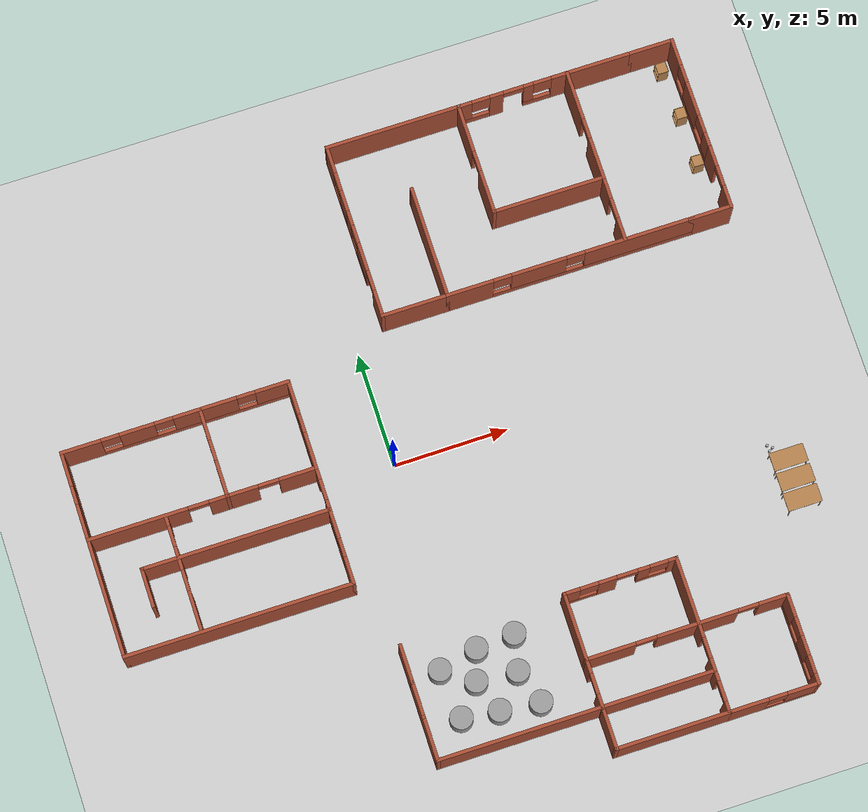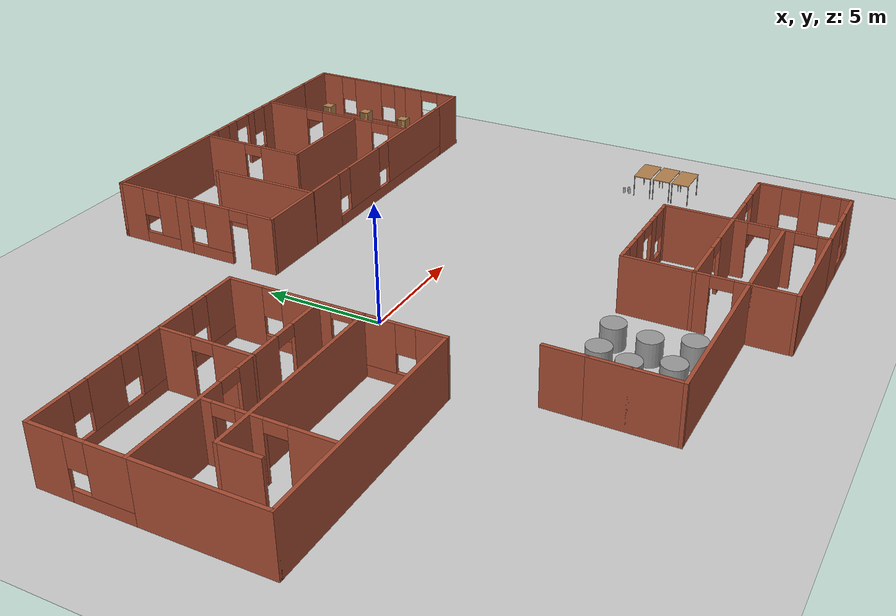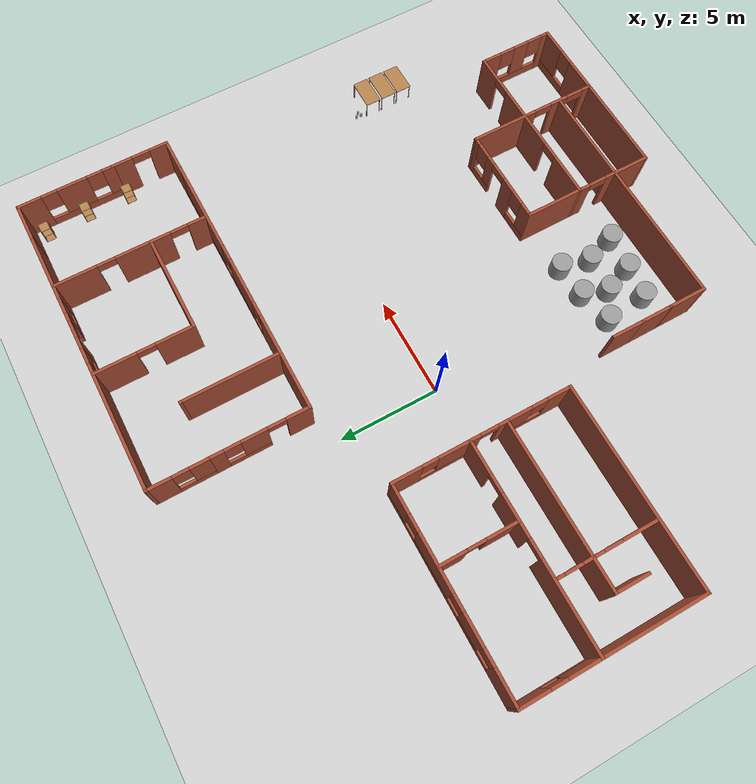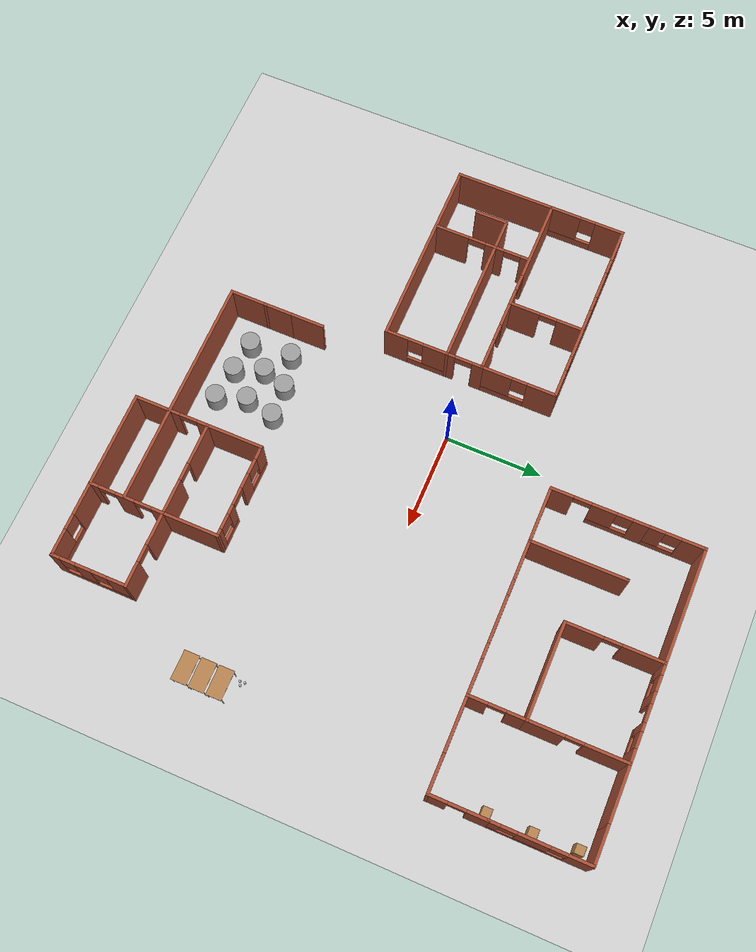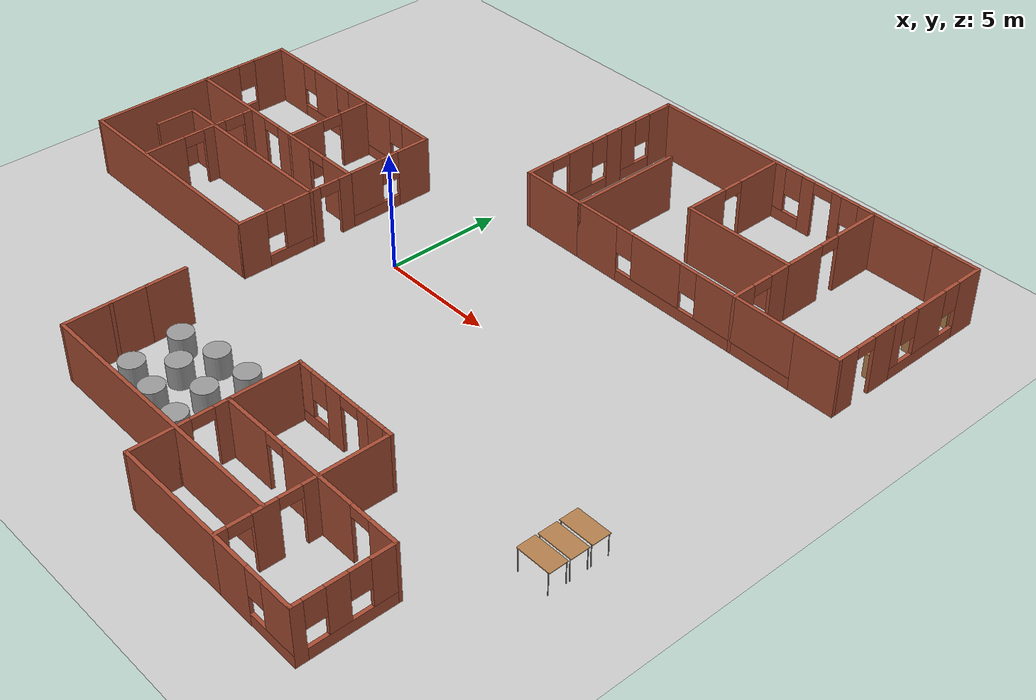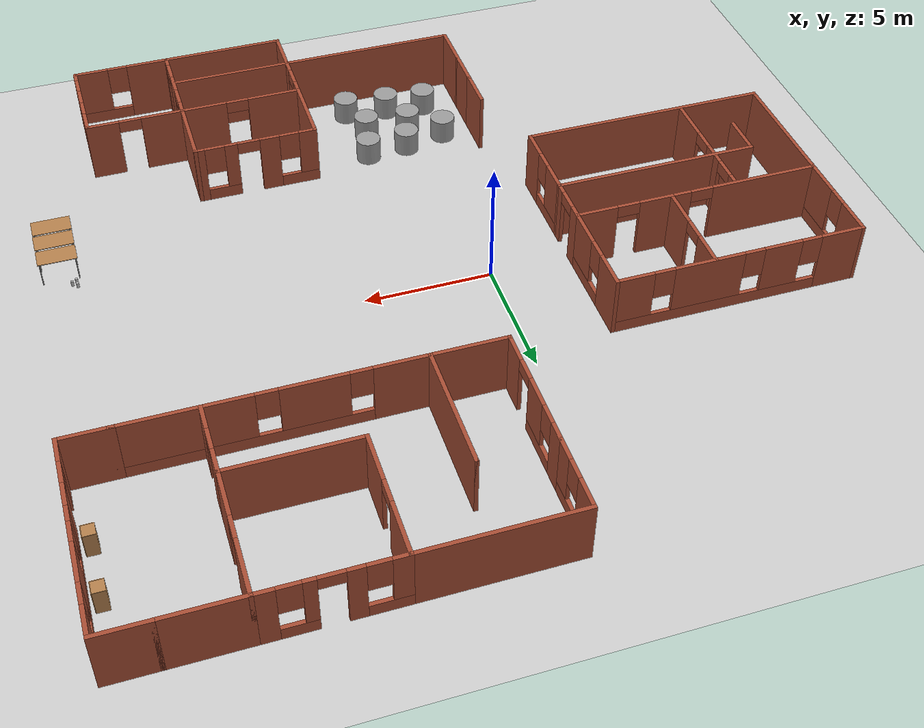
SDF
<sdf version="1.7">
 <world name="default">
  <light name="sun" type="directional">
   <pose>0 0 10 0 -0 0</pose>
   <diffuse>0.8 0.8 0.8 1</diffuse>
   <specular>0.2 0.2 0.2 1</specular>
   <attenuation>
    <range>1000</range>
    <constant>0.9</constant>
    <linear>0.01</linear>
    <quadratic>0.001</quadratic>
   </attenuation>
   <direction>-0.5 0.1 -0.9</direction>
   <spot><inner_angle>0</inner_angle><outer_angle>0</outer_angle><falloff>0</falloff></spot>
  </light>
  <model name="ground_plane">
   <static>1</static>
   <link name="link">
    <collision name="collision">
     <geometry><plane><normal>0 0 1</normal><size>100 100</size></plane></geometry>
     <surface><friction><ode><mu>100</mu><mu2>50</mu2></ode></friction></surface>
    </collision>
    <visual name="visual">
     <cast_shadows>0</cast_shadows>
     <geometry><plane><normal>0 0 1</normal><size>100 100</size></plane></geometry>
     <material>
      <script><uri>file://media/materials/scripts/gazebo.material</uri><name>Gazebo/Grey</name></script>
     </material>
    </visual>
   </link>
  </model>
  <gravity>0 0 -9.8</gravity>
  <magnetic_field>6e-06 2.3e-05 -4.2e-05</magnetic_field>
  <atmosphere type="adiabatic"/>
  <physics type="ode">
   <max_step_size>0.001</max_step_size>
   <real_time_factor>1</real_time_factor>
   <real_time_update_rate>1000</real_time_update_rate>
  </physics>
  <scene><ambient>0.85 0.5 0.125 1</ambient><background>0.7 0.7 0.7 1</background><shadows>1</shadows></scene>
  <spherical_coordinates>
   <surface_model>EARTH_WGS84</surface_model>
   <latitude_deg>0</latitude_deg>
   <longitude_deg>0</longitude_deg>
   <elevation>0</elevation>
   <heading_deg>0</heading_deg>
  </spherical_coordinates>
  <model name="Brick_house3">
   <pose>-3.01773 -0.204708 0 0 -0 0</pose>
   <link name="Wall_11">
    <pose>-10.0574 2.55 0 0 -0 -1.5708</pose>
    <visual name="Wall_11_Visual_0">
     <pose>-1.22598 0 1.25 0 -0 0</pose>
     <geometry><box><size>1.54805 0.15 2.5</size></box></geometry>
     <material>
      <script><uri>file://media/materials/scripts/gazebo.material</uri><name>Gazebo/Bricks</name></script>
      <ambient>1 1 1 1</ambient>
     </material>
     <meta><layer>0</layer></meta>
    </visual>
    <collision name="Wall_11_Collision_0">
     <geometry><box><size>1.54805 0.15 2.5</size></box></geometry>
     <pose>-1.22598 0 1.25 0 -0 0</pose>
    </collision>
    <visual name="Wall_11_Visual_1">
     <pose>0.774024 0 0.25 0 -0 0</pose>
     <geometry><box><size>2.45195 0.15 0.5</size></box></geometry>
     <material>
      <script><uri>file://media/materials/scripts/gazebo.material</uri><name>Gazebo/Bricks</name></script>
      <ambient>1 1 1 1</ambient>
     </material>
     <meta><layer>0</layer></meta>
    </visual>
    <collision name="Wall_11_Collision_1">
     <geometry><box><size>2.45195 0.15 0.5</size></box></geometry>
     <pose>0.774024 0 0.25 0 -0 0</pose>
    </collision>
    <visual name="Wall_11_Visual_2">
     <pose>1.17402 0 1.5 0 -0 0</pose>
     <geometry><box><size>1.65195 0.15 2</size></box></geometry>
     <material>
      <script><uri>file://media/materials/scripts/gazebo.material</uri><name>Gazebo/Bricks</name></script>
      <ambient>1 1 1 1</ambient>
     </material>
     <meta><layer>0</layer></meta>
    </visual>
    <collision name="Wall_11_Collision_2">
     <geometry><box><size>1.65195 0.15 2</size></box></geometry>
     <pose>1.17402 0 1.5 0 -0 0</pose>
    </collision>
    <visual name="Wall_11_Visual_3">
     <pose>-0.051953 0 1.9 0 -0 0</pose>
     <geometry><box><size>0.8 0.15 1.2</size></box></geometry>
     <material>
      <script><uri>file://media/materials/scripts/gazebo.material</uri><name>Gazebo/Bricks</name></script>
      <ambient>1 1 1 1</ambient>
     </material>
     <meta><layer>0</layer></meta>
    </visual>
    <collision name="Wall_11_Collision_3">
     <geometry><box><size>0.8 0.15 1.2</size></box></geometry>
     <pose>-0.051953 0 1.9 0 -0 0</pose>
    </collision>
   </link>
   <link name="Wall_12">
    <pose>-7.05736 0.625 0 0 -0 0</pose>
    <visual name="Wall_12_Visual_0">
     <pose>-0.888053 0 1.25 0 -0 0</pose>
     <geometry><box><size>4.3739 0.15 2.5</size></box></geometry>
     <material>
      <script><uri>file://media/materials/scripts/gazebo.material</uri><name>Gazebo/Bricks</name></script>
      <ambient>1 1 1 1</ambient>
     </material>
     <meta><layer>0</layer></meta>
    </visual>
    <collision name="Wall_12_Collision_0">
     <geometry><box><size>4.3739 0.15 2.5</size></box></geometry>
     <pose>-0.888053 0 1.25 0 -0 0</pose>
    </collision>
    <visual name="Wall_12_Visual_1">
     <pose>2.63695 0 1.25 0 -0 0</pose>
     <geometry><box><size>0.876105 0.15 2.5</size></box></geometry>
     <material>
      <script><uri>file://media/materials/scripts/gazebo.material</uri><name>Gazebo/Bricks</name></script>
      <ambient>1 1 1 1</ambient>
     </material>
     <meta><layer>0</layer></meta>
    </visual>
    <collision name="Wall_12_Collision_1">
     <geometry><box><size>0.876105 0.15 2.5</size></box></geometry>
     <pose>2.63695 0 1.25 0 -0 0</pose>
    </collision>
    <visual name="Wall_12_Visual_2">
     <pose>1.7489 0 2.25 0 -0 0</pose>
     <geometry><box><size>0.9 0.15 0.5</size></box></geometry>
     <material>
      <script><uri>file://media/materials/scripts/gazebo.material</uri><name>Gazebo/Bricks</name></script>
      <ambient>1 1 1 1</ambient>
     </material>
     <meta><layer>0</layer></meta>
    </visual>
    <collision name="Wall_12_Collision_2">
     <geometry><box><size>0.9 0.15 0.5</size></box></geometry>
     <pose>1.7489 0 2.25 0 -0 0</pose>
    </collision>
   </link>
   <link name="Wall_14">
    <pose>-0.207361 -0.3 0 0 -0 -1.5708</pose>
    <visual name="Wall_14_Visual_0">
     <pose>-0.702988 0 1.25 0 -0 0</pose>
     <geometry><box><size>0.594024 0.15 2.5</size></box></geometry>
     <material>
      <script><uri>file://media/materials/scripts/gazebo.material</uri><name>Gazebo/Bricks</name></script>
      <ambient>1 1 1 1</ambient>
     </material>
     <meta><layer>0</layer></meta>
    </visual>
    <collision name="Wall_14_Collision_0">
     <geometry><box><size>0.594024 0.15 2.5</size></box></geometry>
     <pose>-0.702988 0 1.25 0 -0 0</pose>
    </collision>
    <visual name="Wall_14_Visual_1">
     <pose>0.747012 0 1.25 0 -0 0</pose>
     <geometry><box><size>0.505976 0.15 2.5</size></box></geometry>
     <material>
      <script><uri>file://media/materials/scripts/gazebo.material</uri><name>Gazebo/Bricks</name></script>
      <ambient>1 1 1 1</ambient>
     </material>
     <meta><layer>0</layer></meta>
    </visual>
    <collision name="Wall_14_Collision_1">
     <geometry><box><size>0.505976 0.15 2.5</size></box></geometry>
     <pose>0.747012 0 1.25 0 -0 0</pose>
    </collision>
    <visual name="Wall_14_Visual_2">
     <pose>0.044024 0 2.25 0 -0 0</pose>
     <geometry><box><size>0.9 0.15 0.5</size></box></geometry>
     <material>
      <script><uri>file://media/materials/scripts/gazebo.material</uri><name>Gazebo/Bricks</name></script>
      <ambient>1 1 1 1</ambient>
     </material>
     <meta><layer>0</layer></meta>
    </visual>
    <collision name="Wall_14_Collision_2">
     <geometry><box><size>0.9 0.15 0.5</size></box></geometry>
     <pose>0.044024 0 2.25 0 -0 0</pose>
    </collision>
   </link>
   <link name="Wall_15">
    <collision name="Wall_15_Collision">
     <geometry><box><size>8.25 0.15 2.5</size></box></geometry>
     <pose>0 0 1.25 0 -0 0</pose>
    </collision>
    <visual name="Wall_15_Visual">
     <pose>0 0 1.25 0 -0 0</pose>
     <geometry><box><size>8.25 0.15 2.5</size></box></geometry>
     <material>
      <script><uri>file://media/materials/scripts/gazebo.material</uri><name>Gazebo/Bricks</name></script>
      <ambient>1 1 1 1</ambient>
     </material>
     <meta><layer>0</layer></meta>
    </visual>
    <pose>-4.25736 -1.225 0 0 -0 3.14159</pose>
   </link>
   <link name="Wall_16">
    <collision name="Wall_16_Collision">
     <geometry><box><size>1.75 0.15 2.5</size></box></geometry>
     <pose>0 0 1.25 0 -0 0</pose>
    </collision>
    <visual name="Wall_16_Visual">
     <pose>0 0 1.25 0 -0 0</pose>
     <geometry><box><size>1.75 0.15 2.5</size></box></geometry>
     <material>
      <script><uri>file://media/materials/scripts/gazebo.material</uri><name>Gazebo/Bricks</name></script>
      <ambient>1 1 1 1</ambient>
     </material>
     <meta><layer>0</layer></meta>
    </visual>
    <pose>-8.30736 -2.025 0 0 -0 -1.5708</pose>
   </link>
   <link name="Wall_18">
    <collision name="Wall_18_Collision">
     <geometry><box><size>5.25 0.15 2.5</size></box></geometry>
     <pose>0 0 1.25 0 -0 0</pose>
    </collision>
    <visual name="Wall_18_Visual">
     <pose>0 0 1.25 0 -0 0</pose>
     <geometry><box><size>5.25 0.15 2.5</size></box></geometry>
     <material>
      <script><uri>file://media/materials/scripts/gazebo.material</uri><name>Gazebo/Bricks</name></script>
      <ambient>1 1 1 1</ambient>
     </material>
     <meta><layer>0</layer></meta>
    </visual>
    <pose>-10.0574 -1.925 0 0 -0 -1.5708</pose>
   </link>
   <link name="Wall_19">
    <collision name="Wall_19_Collision">
     <geometry><box><size>10 0.15 2.5</size></box></geometry>
     <pose>0 0 1.25 0 -0 0</pose>
    </collision>
    <visual name="Wall_19_Visual">
     <pose>0 0 1.25 0 -0 0</pose>
     <geometry><box><size>10 0.15 2.5</size></box></geometry>
     <material>
      <script><uri>file://media/materials/scripts/gazebo.material</uri><name>Gazebo/Bricks</name></script>
      <ambient>1 1 1 1</ambient>
     </material>
     <meta><layer>0</layer></meta>
    </visual>
    <pose>-5.13236 -4.475 0 0 -0 0</pose>
   </link>
   <link name="Wall_20">
    <pose>-0.207361 -2.85 0 0 -0 1.5708</pose>
    <visual name="Wall_20_Visual_0">
     <pose>-1.07906 0 1.25 0 -0 0</pose>
     <geometry><box><size>1.24188 0.15 2.5</size></box></geometry>
     <material>
      <script><uri>file://media/materials/scripts/gazebo.material</uri><name>Gazebo/Bricks</name></script>
      <ambient>1 1 1 1</ambient>
     </material>
     <meta><layer>0</layer></meta>
    </visual>
    <collision name="Wall_20_Collision_0">
     <geometry><box><size>1.24188 0.15 2.5</size></box></geometry>
     <pose>-1.07906 0 1.25 0 -0 0</pose>
    </collision>
    <visual name="Wall_20_Visual_1">
     <pose>0.620943 0 0.25 0 -0 0</pose>
     <geometry><box><size>2.15812 0.15 0.5</size></box></geometry>
     <material>
      <script><uri>file://media/materials/scripts/gazebo.material</uri><name>Gazebo/Bricks</name></script>
      <ambient>1 1 1 1</ambient>
     </material>
     <meta><layer>0</layer></meta>
    </visual>
    <collision name="Wall_20_Collision_1">
     <geometry><box><size>2.15812 0.15 0.5</size></box></geometry>
     <pose>0.620943 0 0.25 0 -0 0</pose>
    </collision>
    <visual name="Wall_20_Visual_2">
     <pose>1.02094 0 1.5 0 -0 0</pose>
     <geometry><box><size>1.35811 0.15 2</size></box></geometry>
     <material>
      <script><uri>file://media/materials/scripts/gazebo.material</uri><name>Gazebo/Bricks</name></script>
      <ambient>1 1 1 1</ambient>
     </material>
     <meta><layer>0</layer></meta>
    </visual>
    <collision name="Wall_20_Collision_2">
     <geometry><box><size>1.35811 0.15 2</size></box></geometry>
     <pose>1.02094 0 1.5 0 -0 0</pose>
    </collision>
    <visual name="Wall_20_Visual_3">
     <pose>-0.058115 0 1.9 0 -0 0</pose>
     <geometry><box><size>0.8 0.15 1.2</size></box></geometry>
     <material>
      <script><uri>file://media/materials/scripts/gazebo.material</uri><name>Gazebo/Bricks</name></script>
      <ambient>1 1 1 1</ambient>
     </material>
     <meta><layer>0</layer></meta>
    </visual>
    <collision name="Wall_20_Collision_3">
     <geometry><box><size>0.8 0.15 1.2</size></box></geometry>
     <pose>-0.058115 0 1.9 0 -0 0</pose>
    </collision>
   </link>
   <link name="Wall_22">
    <pose>-6.73111 -1.94178 0 0 -0 1.5708</pose>
    <visual name="Wall_22_Visual_0">
     <pose>-1.61465 0 1.25 0 -0 0</pose>
     <geometry><box><size>1.7707 0.15 2.5</size></box></geometry>
     <material>
      <script><uri>file://media/materials/scripts/gazebo.material</uri><name>Gazebo/Bricks</name></script>
      <ambient>1 1 1 1</ambient>
     </material>
     <meta><layer>0</layer></meta>
    </visual>
    <collision name="Wall_22_Collision_0">
     <geometry><box><size>1.7707 0.15 2.5</size></box></geometry>
     <pose>-1.61465 0 1.25 0 -0 0</pose>
    </collision>
    <visual name="Wall_22_Visual_1">
     <pose>0.686508 0 1.25 0 -0 0</pose>
     <geometry><box><size>1.03161 0.15 2.5</size></box></geometry>
     <material>
      <script><uri>file://media/materials/scripts/gazebo.material</uri><name>Gazebo/Bricks</name></script>
      <ambient>1 1 1 1</ambient>
     </material>
     <meta><layer>0</layer></meta>
    </visual>
    <collision name="Wall_22_Collision_1">
     <geometry><box><size>1.03161 0.15 2.5</size></box></geometry>
     <pose>0.686508 0 1.25 0 -0 0</pose>
    </collision>
    <visual name="Wall_22_Visual_2">
     <pose>2.30116 0 1.25 0 -0 0</pose>
     <geometry><box><size>0.397688 0.15 2.5</size></box></geometry>
     <material>
      <script><uri>file://media/materials/scripts/gazebo.material</uri><name>Gazebo/Bricks</name></script>
      <ambient>1 1 1 1</ambient>
     </material>
     <meta><layer>0</layer></meta>
    </visual>
    <collision name="Wall_22_Collision_2">
     <geometry><box><size>0.397688 0.15 2.5</size></box></geometry>
     <pose>2.30116 0 1.25 0 -0 0</pose>
    </collision>
    <visual name="Wall_22_Visual_3">
     <pose>-0.279296 0 2.25 0 -0 0</pose>
     <geometry><box><size>0.9 0.15 0.5</size></box></geometry>
     <material>
      <script><uri>file://media/materials/scripts/gazebo.material</uri><name>Gazebo/Bricks</name></script>
      <ambient>1 1 1 1</ambient>
     </material>
     <meta><layer>0</layer></meta>
    </visual>
    <collision name="Wall_22_Collision_3">
     <geometry><box><size>0.9 0.15 0.5</size></box></geometry>
     <pose>-0.279296 0 2.25 0 -0 0</pose>
    </collision>
    <visual name="Wall_22_Visual_4">
     <pose>1.65231 0 2.25 0 -0 0</pose>
     <geometry><box><size>0.9 0.15 0.5</size></box></geometry>
     <material>
      <script><uri>file://media/materials/scripts/gazebo.material</uri><name>Gazebo/Bricks</name></script>
      <ambient>1 1 1 1</ambient>
     </material>
     <meta><layer>0</layer></meta>
    </visual>
    <collision name="Wall_22_Collision_4">
     <geometry><box><size>0.9 0.15 0.5</size></box></geometry>
     <pose>1.65231 0 2.25 0 -0 0</pose>
    </collision>
   </link>
   <link name="Wall_6">
    <pose>-5.13236 4.475 0 0 -0 0</pose>
    <visual name="Wall_6_Visual_0">
     <pose>-4.11101 0 1.25 0 -0 0</pose>
     <geometry><box><size>1.77797 0.15 2.5</size></box></geometry>
     <material>
      <script><uri>file://media/materials/scripts/gazebo.material</uri><name>Gazebo/Bricks</name></script>
      <ambient>1 1 1 1</ambient>
     </material>
     <meta><layer>0</layer></meta>
    </visual>
    <collision name="Wall_6_Collision_0">
     <geometry><box><size>1.77797 0.15 2.5</size></box></geometry>
     <pose>-4.11101 0 1.25 0 -0 0</pose>
    </collision>
    <visual name="Wall_6_Visual_1">
     <pose>0.888986 0 0.25 0 -0 0</pose>
     <geometry><box><size>8.22203 0.15 0.5</size></box></geometry>
     <material>
      <script><uri>file://media/materials/scripts/gazebo.material</uri><name>Gazebo/Bricks</name></script>
      <ambient>1 1 1 1</ambient>
     </material>
     <meta><layer>0</layer></meta>
    </visual>
    <collision name="Wall_6_Collision_1">
     <geometry><box><size>8.22203 0.15 0.5</size></box></geometry>
     <pose>0.888986 0 0.25 0 -0 0</pose>
    </collision>
    <visual name="Wall_6_Visual_2">
     <pose>-1.66273 0 1.5 0 -0 0</pose>
     <geometry><box><size>1.51859 0.15 2</size></box></geometry>
     <material>
      <script><uri>file://media/materials/scripts/gazebo.material</uri><name>Gazebo/Bricks</name></script>
      <ambient>1 1 1 1</ambient>
     </material>
     <meta><layer>0</layer></meta>
    </visual>
    <collision name="Wall_6_Collision_2">
     <geometry><box><size>1.51859 0.15 2</size></box></geometry>
     <pose>-1.66273 0 1.5 0 -0 0</pose>
    </collision>
    <visual name="Wall_6_Visual_3">
     <pose>1.28324 0 1.5 0 -0 0</pose>
     <geometry><box><size>2.77336 0.15 2</size></box></geometry>
     <material>
      <script><uri>file://media/materials/scripts/gazebo.material</uri><name>Gazebo/Bricks</name></script>
      <ambient>1 1 1 1</ambient>
     </material>
     <meta><layer>0</layer></meta>
    </visual>
    <collision name="Wall_6_Collision_3">
     <geometry><box><size>2.77336 0.15 2</size></box></geometry>
     <pose>1.28324 0 1.5 0 -0 0</pose>
    </collision>
    <visual name="Wall_6_Visual_4">
     <pose>4.23496 0 1.5 0 -0 0</pose>
     <geometry><box><size>1.53008 0.15 2</size></box></geometry>
     <material>
      <script><uri>file://media/materials/scripts/gazebo.material</uri><name>Gazebo/Bricks</name></script>
      <ambient>1 1 1 1</ambient>
     </material>
     <meta><layer>0</layer></meta>
    </visual>
    <collision name="Wall_6_Collision_4">
     <geometry><box><size>1.53008 0.15 2</size></box></geometry>
     <pose>4.23496 0 1.5 0 -0 0</pose>
    </collision>
    <visual name="Wall_6_Visual_5">
     <pose>-2.82203 0 1.9 0 -0 0</pose>
     <geometry><box><size>0.8 0.15 1.2</size></box></geometry>
     <material>
      <script><uri>file://media/materials/scripts/gazebo.material</uri><name>Gazebo/Bricks</name></script>
      <ambient>1 1 1 1</ambient>
     </material>
     <meta><layer>0</layer></meta>
    </visual>
    <collision name="Wall_6_Collision_5">
     <geometry><box><size>0.8 0.15 1.2</size></box></geometry>
     <pose>-2.82203 0 1.9 0 -0 0</pose>
    </collision>
    <visual name="Wall_6_Visual_6">
     <pose>-0.503436 0 1.9 0 -0 0</pose>
     <geometry><box><size>0.8 0.15 1.2</size></box></geometry>
     <material>
      <script><uri>file://media/materials/scripts/gazebo.material</uri><name>Gazebo/Bricks</name></script>
      <ambient>1 1 1 1</ambient>
     </material>
     <meta><layer>0</layer></meta>
    </visual>
    <collision name="Wall_6_Collision_6">
     <geometry><box><size>0.8 0.15 1.2</size></box></geometry>
     <pose>-0.503436 0 1.9 0 -0 0</pose>
    </collision>
    <visual name="Wall_6_Visual_7">
     <pose>3.06992 0 1.9 0 -0 0</pose>
     <geometry><box><size>0.8 0.15 1.2</size></box></geometry>
     <material>
      <script><uri>file://media/materials/scripts/gazebo.material</uri><name>Gazebo/Bricks</name></script>
      <ambient>1 1 1 1</ambient>
     </material>
     <meta><layer>0</layer></meta>
    </visual>
    <collision name="Wall_6_Collision_7">
     <geometry><box><size>0.8 0.15 1.2</size></box></geometry>
     <pose>3.06992 0 1.9 0 -0 0</pose>
    </collision>
   </link>
   <link name="Wall_7">
    <pose>-0.207361 2.55 0 0 -0 -1.5708</pose>
    <visual name="Wall_7_Visual_0">
     <pose>-1.22598 0 1.25 0 -0 0</pose>
     <geometry><box><size>1.54805 0.15 2.5</size></box></geometry>
     <material>
      <script><uri>file://media/materials/scripts/gazebo.material</uri><name>Gazebo/Bricks</name></script>
      <ambient>1 1 1 1</ambient>
     </material>
     <meta><layer>0</layer></meta>
    </visual>
    <collision name="Wall_7_Collision_0">
     <geometry><box><size>1.54805 0.15 2.5</size></box></geometry>
     <pose>-1.22598 0 1.25 0 -0 0</pose>
    </collision>
    <visual name="Wall_7_Visual_1">
     <pose>0.774024 0 0.25 0 -0 0</pose>
     <geometry><box><size>2.45195 0.15 0.5</size></box></geometry>
     <material>
      <script><uri>file://media/materials/scripts/gazebo.material</uri><name>Gazebo/Bricks</name></script>
      <ambient>1 1 1 1</ambient>
     </material>
     <meta><layer>0</layer></meta>
    </visual>
    <collision name="Wall_7_Collision_1">
     <geometry><box><size>2.45195 0.15 0.5</size></box></geometry>
     <pose>0.774024 0 0.25 0 -0 0</pose>
    </collision>
    <visual name="Wall_7_Visual_2">
     <pose>1.17402 0 1.5 0 -0 0</pose>
     <geometry><box><size>1.65195 0.15 2</size></box></geometry>
     <material>
      <script><uri>file://media/materials/scripts/gazebo.material</uri><name>Gazebo/Bricks</name></script>
      <ambient>1 1 1 1</ambient>
     </material>
     <meta><layer>0</layer></meta>
    </visual>
    <collision name="Wall_7_Collision_2">
     <geometry><box><size>1.65195 0.15 2</size></box></geometry>
     <pose>1.17402 0 1.5 0 -0 0</pose>
    </collision>
    <visual name="Wall_7_Visual_3">
     <pose>-0.051953 0 1.9 0 -0 0</pose>
     <geometry><box><size>0.8 0.15 1.2</size></box></geometry>
     <material>
      <script><uri>file://media/materials/scripts/gazebo.material</uri><name>Gazebo/Bricks</name></script>
      <ambient>1 1 1 1</ambient>
     </material>
     <meta><layer>0</layer></meta>
    </visual>
    <collision name="Wall_7_Collision_3">
     <geometry><box><size>0.8 0.15 1.2</size></box></geometry>
     <pose>-0.051953 0 1.9 0 -0 0</pose>
    </collision>
   </link>
   <link name="Wall_8">
    <pose>-2.13236 0.625 0 0 -0 3.14159</pose>
    <visual name="Wall_8_Visual_0">
     <pose>-1.15085 0 1.25 0 -0 0</pose>
     <geometry><box><size>1.6983 0.15 2.5</size></box></geometry>
     <material>
      <script><uri>file://media/materials/scripts/gazebo.material</uri><name>Gazebo/Bricks</name></script>
      <ambient>1 1 1 1</ambient>
     </material>
     <meta><layer>0</layer></meta>
    </visual>
    <collision name="Wall_8_Collision_0">
     <geometry><box><size>1.6983 0.15 2.5</size></box></geometry>
     <pose>-1.15085 0 1.25 0 -0 0</pose>
    </collision>
    <visual name="Wall_8_Visual_1">
     <pose>1.29915 0 1.25 0 -0 0</pose>
     <geometry><box><size>1.4017 0.15 2.5</size></box></geometry>
     <material>
      <script><uri>file://media/materials/scripts/gazebo.material</uri><name>Gazebo/Bricks</name></script>
      <ambient>1 1 1 1</ambient>
     </material>
     <meta><layer>0</layer></meta>
    </visual>
    <collision name="Wall_8_Collision_1">
     <geometry><box><size>1.4017 0.15 2.5</size></box></geometry>
     <pose>1.29915 0 1.25 0 -0 0</pose>
    </collision>
    <visual name="Wall_8_Visual_2">
     <pose>0.148296 0 2.25 0 -0 0</pose>
     <geometry><box><size>0.9 0.15 0.5</size></box></geometry>
     <material>
      <script><uri>file://media/materials/scripts/gazebo.material</uri><name>Gazebo/Bricks</name></script>
      <ambient>1 1 1 1</ambient>
     </material>
     <meta><layer>0</layer></meta>
    </visual>
    <collision name="Wall_8_Collision_2">
     <geometry><box><size>0.9 0.15 0.5</size></box></geometry>
     <pose>0.148296 0 2.25 0 -0 0</pose>
    </collision>
   </link>
   <link name="Wall_9">
    <pose>-4.05736 2.55 0 0 -0 1.5708</pose>
    <visual name="Wall_9_Visual_0">
     <pose>-1.17175 0 1.25 0 -0 0</pose>
     <geometry><box><size>1.65651 0.15 2.5</size></box></geometry>
     <material>
      <script><uri>file://media/materials/scripts/gazebo.material</uri><name>Gazebo/Bricks</name></script>
      <ambient>1 1 1 1</ambient>
     </material>
     <meta><layer>0</layer></meta>
    </visual>
    <collision name="Wall_9_Collision_0">
     <geometry><box><size>1.65651 0.15 2.5</size></box></geometry>
     <pose>-1.17175 0 1.25 0 -0 0</pose>
    </collision>
    <visual name="Wall_9_Visual_1">
     <pose>1.27825 0 1.25 0 -0 0</pose>
     <geometry><box><size>1.44349 0.15 2.5</size></box></geometry>
     <material>
      <script><uri>file://media/materials/scripts/gazebo.material</uri><name>Gazebo/Bricks</name></script>
      <ambient>1 1 1 1</ambient>
     </material>
     <meta><layer>0</layer></meta>
    </visual>
    <collision name="Wall_9_Collision_1">
     <geometry><box><size>1.44349 0.15 2.5</size></box></geometry>
     <pose>1.27825 0 1.25 0 -0 0</pose>
    </collision>
    <visual name="Wall_9_Visual_2">
     <pose>0.106508 0 2.25 0 -0 0</pose>
     <geometry><box><size>0.9 0.15 0.5</size></box></geometry>
     <material>
      <script><uri>file://media/materials/scripts/gazebo.material</uri><name>Gazebo/Bricks</name></script>
      <ambient>1 1 1 1</ambient>
     </material>
     <meta><layer>0</layer></meta>
    </visual>
    <collision name="Wall_9_Collision_2">
     <geometry><box><size>0.9 0.15 0.5</size></box></geometry>
     <pose>0.106508 0 2.25 0 -0 0</pose>
    </collision>
   </link>
   <static>1</static>
  </model>
  <model name="brick_house2">
   <pose>5.68495 -9.98238 0 0 -0 0</pose>
   <link name="Wall_45">
    <pose>1.60155 -0.643048 0 0 -0 0</pose>
    <visual name="Wall_45_Visual_0">
     <pose>-1.39493 0 1.25 0 -0 0</pose>
     <geometry><box><size>2.21014 0.15 2.5</size></box></geometry>
     <material>
      <script><uri>file://media/materials/scripts/gazebo.material</uri><name>Gazebo/Bricks</name></script>
      <ambient>1 1 1 1</ambient>
     </material>
     <meta><layer>0</layer></meta>
    </visual>
    <collision name="Wall_45_Collision_0">
     <geometry><box><size>2.21014 0.15 2.5</size></box></geometry>
     <pose>-1.39493 0 1.25 0 -0 0</pose>
    </collision>
    <visual name="Wall_45_Visual_1">
     <pose>1.55507 0 1.25 0 -0 0</pose>
     <geometry><box><size>1.88986 0.15 2.5</size></box></geometry>
     <material>
      <script><uri>file://media/materials/scripts/gazebo.material</uri><name>Gazebo/Bricks</name></script>
      <ambient>1 1 1 1</ambient>
     </material>
     <meta><layer>0</layer></meta>
    </visual>
    <collision name="Wall_45_Collision_1">
     <geometry><box><size>1.88986 0.15 2.5</size></box></geometry>
     <pose>1.55507 0 1.25 0 -0 0</pose>
    </collision>
    <visual name="Wall_45_Visual_2">
     <pose>0.160145 0 2.25 0 -0 0</pose>
     <geometry><box><size>0.9 0.15 0.5</size></box></geometry>
     <material>
      <script><uri>file://media/materials/scripts/gazebo.material</uri><name>Gazebo/Bricks</name></script>
      <ambient>1 1 1 1</ambient>
     </material>
     <meta><layer>0</layer></meta>
    </visual>
    <collision name="Wall_45_Collision_2">
     <geometry><box><size>0.9 0.15 0.5</size></box></geometry>
     <pose>0.160145 0 2.25 0 -0 0</pose>
    </collision>
   </link>
   <link name="Wall_46">
    <collision name="Wall_46_Collision">
     <geometry><box><size>3 0.15 2.5</size></box></geometry>
     <pose>0 0 1.25 0 -0 0</pose>
    </collision>
    <visual name="Wall_46_Visual">
     <pose>0 0 1.25 0 -0 0</pose>
     <geometry><box><size>3 0.15 2.5</size></box></geometry>
     <material>
      <script><uri>file://media/materials/scripts/gazebo.material</uri><name>Gazebo/Bricks</name></script>
      <ambient>1 1 1 1</ambient>
     </material>
     <meta><layer>0</layer></meta>
    </visual>
    <pose>4.02655 0.781952 0 0 -0 1.5708</pose>
   </link>
   <link name="Wall_47">
    <pose>1.60155 2.20695 0 0 -0 3.14159</pose>
    <visual name="Wall_47_Visual_0">
     <pose>-2.28479 0 1.25 0 -0 0</pose>
     <geometry><box><size>0.430426 0.15 2.5</size></box></geometry>
     <material>
      <script><uri>file://media/materials/scripts/gazebo.material</uri><name>Gazebo/Bricks</name></script>
      <ambient>1 1 1 1</ambient>
     </material>
     <meta><layer>0</layer></meta>
    </visual>
    <collision name="Wall_47_Collision_0">
     <geometry><box><size>0.430426 0.15 2.5</size></box></geometry>
     <pose>-2.28479 0 1.25 0 -0 0</pose>
    </collision>
    <visual name="Wall_47_Visual_1">
     <pose>0.550959 0 1.25 0 -0 0</pose>
     <geometry><box><size>0.79665 0.15 2.5</size></box></geometry>
     <material>
      <script><uri>file://media/materials/scripts/gazebo.material</uri><name>Gazebo/Bricks</name></script>
      <ambient>1 1 1 1</ambient>
     </material>
     <meta><layer>0</layer></meta>
    </visual>
    <collision name="Wall_47_Collision_1">
     <geometry><box><size>0.79665 0.15 2.5</size></box></geometry>
     <pose>0.550959 0 1.25 0 -0 0</pose>
    </collision>
    <visual name="Wall_47_Visual_2">
     <pose>-1.40847 0 0.25 0 -0 0</pose>
     <geometry><box><size>1.32221 0.15 0.5</size></box></geometry>
     <material>
      <script><uri>file://media/materials/scripts/gazebo.material</uri><name>Gazebo/Bricks</name></script>
      <ambient>1 1 1 1</ambient>
     </material>
     <meta><layer>0</layer></meta>
    </visual>
    <collision name="Wall_47_Collision_2">
     <geometry><box><size>1.32221 0.15 0.5</size></box></geometry>
     <pose>-1.40847 0 0.25 0 -0 0</pose>
    </collision>
    <visual name="Wall_47_Visual_3">
     <pose>1.72464 0 0.25 0 -0 0</pose>
     <geometry><box><size>1.55072 0.15 0.5</size></box></geometry>
     <material>
      <script><uri>file://media/materials/scripts/gazebo.material</uri><name>Gazebo/Bricks</name></script>
      <ambient>1 1 1 1</ambient>
     </material>
     <meta><layer>0</layer></meta>
    </visual>
    <collision name="Wall_47_Collision_3">
     <geometry><box><size>1.55072 0.15 0.5</size></box></geometry>
     <pose>1.72464 0 0.25 0 -0 0</pose>
    </collision>
    <visual name="Wall_47_Visual_4">
     <pose>-1.00847 0 1.5 0 -0 0</pose>
     <geometry><box><size>0.522208 0.15 2</size></box></geometry>
     <material>
      <script><uri>file://media/materials/scripts/gazebo.material</uri><name>Gazebo/Bricks</name></script>
      <ambient>1 1 1 1</ambient>
     </material>
     <meta><layer>0</layer></meta>
    </visual>
    <collision name="Wall_47_Collision_4">
     <geometry><box><size>0.522208 0.15 2</size></box></geometry>
     <pose>-1.00847 0 1.5 0 -0 0</pose>
    </collision>
    <visual name="Wall_47_Visual_5">
     <pose>-1.00847 0 1.5 0 -0 0</pose>
     <geometry><box><size>0.522208 0.15 2</size></box></geometry>
     <material>
      <script><uri>file://media/materials/scripts/gazebo.material</uri><name>Gazebo/Bricks</name></script>
      <ambient>1 1 1 1</ambient>
     </material>
     <meta><layer>0</layer></meta>
    </visual>
    <collision name="Wall_47_Collision_5">
     <geometry><box><size>0.522208 0.15 2</size></box></geometry>
     <pose>-1.00847 0 1.5 0 -0 0</pose>
    </collision>
    <visual name="Wall_47_Visual_6">
     <pose>2.12464 0 1.5 0 -0 0</pose>
     <geometry><box><size>0.750717 0.15 2</size></box></geometry>
     <material>
      <script><uri>file://media/materials/scripts/gazebo.material</uri><name>Gazebo/Bricks</name></script>
      <ambient>1 1 1 1</ambient>
     </material>
     <meta><layer>0</layer></meta>
    </visual>
    <collision name="Wall_47_Collision_6">
     <geometry><box><size>0.750717 0.15 2</size></box></geometry>
     <pose>2.12464 0 1.5 0 -0 0</pose>
    </collision>
    <visual name="Wall_47_Visual_7">
     <pose>-1.66957 0 1.9 0 -0 0</pose>
     <geometry><box><size>0.8 0.15 1.2</size></box></geometry>
     <material>
      <script><uri>file://media/materials/scripts/gazebo.material</uri><name>Gazebo/Bricks</name></script>
      <ambient>1 1 1 1</ambient>
     </material>
     <meta><layer>0</layer></meta>
    </visual>
    <collision name="Wall_47_Collision_7">
     <geometry><box><size>0.8 0.15 1.2</size></box></geometry>
     <pose>-1.66957 0 1.9 0 -0 0</pose>
    </collision>
    <visual name="Wall_47_Visual_8">
     <pose>1.34928 0 1.9 0 -0 0</pose>
     <geometry><box><size>0.8 0.15 1.2</size></box></geometry>
     <material>
      <script><uri>file://media/materials/scripts/gazebo.material</uri><name>Gazebo/Bricks</name></script>
      <ambient>1 1 1 1</ambient>
     </material>
     <meta><layer>0</layer></meta>
    </visual>
    <collision name="Wall_47_Collision_8">
     <geometry><box><size>0.8 0.15 1.2</size></box></geometry>
     <pose>1.34928 0 1.9 0 -0 0</pose>
    </collision>
    <visual name="Wall_47_Visual_9">
     <pose>-0.297366 0 2.25 0 -0 0</pose>
     <geometry><box><size>0.9 0.15 0.5</size></box></geometry>
     <material>
      <script><uri>file://media/materials/scripts/gazebo.material</uri><name>Gazebo/Bricks</name></script>
      <ambient>1 1 1 1</ambient>
     </material>
     <meta><layer>0</layer></meta>
    </visual>
    <collision name="Wall_47_Collision_9">
     <geometry><box><size>0.9 0.15 0.5</size></box></geometry>
     <pose>-0.297366 0 2.25 0 -0 0</pose>
    </collision>
    <visual name="Wall_47_Visual_10">
     <pose>-0.297366 0 2.25 0 -0 0</pose>
     <geometry><box><size>0.9 0.15 0.5</size></box></geometry>
     <material>
      <script><uri>file://media/materials/scripts/gazebo.material</uri><name>Gazebo/Bricks</name></script>
      <ambient>1 1 1 1</ambient>
     </material>
     <meta><layer>0</layer></meta>
    </visual>
    <collision name="Wall_47_Collision_10">
     <geometry><box><size>0.9 0.15 0.5</size></box></geometry>
     <pose>-0.297366 0 2.25 0 -0 0</pose>
    </collision>
   </link>
   <link name="Wall_48">
    <collision name="Wall_48_Collision">
     <geometry><box><size>0.16 0.15 2.5</size></box></geometry>
     <pose>0 0 1.25 0 -0 0</pose>
    </collision>
    <visual name="Wall_48_Visual">
     <pose>0 0 1.25 0 -0 0</pose>
     <geometry><box><size>0.16 0.15 2.5</size></box></geometry>
     <material>
      <script><uri>file://media/materials/scripts/gazebo.material</uri><name>Gazebo/Bricks</name></script>
      <ambient>1 1 1 1</ambient>
     </material>
     <meta><layer>0</layer></meta>
    </visual>
    <pose>-0.818451 2.20695 0 0 -0 0</pose>
   </link>
   <link name="Wall_50">
    <collision name="Wall_50_Collision">
     <geometry><box><size>3 0.15 2.5</size></box></geometry>
     <pose>0 0 1.25 0 -0 0</pose>
    </collision>
    <visual name="Wall_50_Visual">
     <pose>0 0 1.25 0 -0 0</pose>
     <geometry><box><size>3 0.15 2.5</size></box></geometry>
     <material>
      <script><uri>file://media/materials/scripts/gazebo.material</uri><name>Gazebo/Bricks</name></script>
      <ambient>1 1 1 1</ambient>
     </material>
     <meta><layer>0</layer></meta>
    </visual>
    <pose>-0.823451 0.781952 0 0 -0 1.5708</pose>
   </link>
   <link name="Wall_52">
    <pose>5.95155 -0.643048 0 0 -0 0</pose>
    <visual name="Wall_52_Visual_0">
     <pose>-1.11296 0 1.25 0 -0 0</pose>
     <geometry><box><size>1.77408 0.15 2.5</size></box></geometry>
     <material>
      <script><uri>file://media/materials/scripts/gazebo.material</uri><name>Gazebo/Bricks</name></script>
      <ambient>1 1 1 1</ambient>
     </material>
     <meta><layer>0</layer></meta>
    </visual>
    <collision name="Wall_52_Collision_0">
     <geometry><box><size>1.77408 0.15 2.5</size></box></geometry>
     <pose>-1.11296 0 1.25 0 -0 0</pose>
    </collision>
    <visual name="Wall_52_Visual_1">
     <pose>1.33704 0 1.25 0 -0 0</pose>
     <geometry><box><size>1.32592 0.15 2.5</size></box></geometry>
     <material>
      <script><uri>file://media/materials/scripts/gazebo.material</uri><name>Gazebo/Bricks</name></script>
      <ambient>1 1 1 1</ambient>
     </material>
     <meta><layer>0</layer></meta>
    </visual>
    <collision name="Wall_52_Collision_1">
     <geometry><box><size>1.32592 0.15 2.5</size></box></geometry>
     <pose>1.33704 0 1.25 0 -0 0</pose>
    </collision>
    <visual name="Wall_52_Visual_2">
     <pose>0.22408 0 2.25 0 -0 0</pose>
     <geometry><box><size>0.9 0.15 0.5</size></box></geometry>
     <material>
      <script><uri>file://media/materials/scripts/gazebo.material</uri><name>Gazebo/Bricks</name></script>
      <ambient>1 1 1 1</ambient>
     </material>
     <meta><layer>0</layer></meta>
    </visual>
    <collision name="Wall_52_Collision_2">
     <geometry><box><size>0.9 0.15 0.5</size></box></geometry>
     <pose>0.22408 0 2.25 0 -0 0</pose>
    </collision>
   </link>
   <link name="Wall_54">
    <pose>4.02655 -2.56805 0 0 -0 -1.5708</pose>
    <visual name="Wall_54_Visual_0">
     <pose>-1.65357 0 1.25 0 -0 0</pose>
     <geometry><box><size>0.692853 0.15 2.5</size></box></geometry>
     <material>
      <script><uri>file://media/materials/scripts/gazebo.material</uri><name>Gazebo/Bricks</name></script>
      <ambient>1 1 1 1</ambient>
     </material>
     <meta><layer>0</layer></meta>
    </visual>
    <collision name="Wall_54_Collision_0">
     <geometry><box><size>0.692853 0.15 2.5</size></box></geometry>
     <pose>-1.65357 0 1.25 0 -0 0</pose>
    </collision>
    <visual name="Wall_54_Visual_1">
     <pose>0.080528 0 1.25 0 -0 0</pose>
     <geometry><box><size>0.97535 0.15 2.5</size></box></geometry>
     <material>
      <script><uri>file://media/materials/scripts/gazebo.material</uri><name>Gazebo/Bricks</name></script>
      <ambient>1 1 1 1</ambient>
     </material>
     <meta><layer>0</layer></meta>
    </visual>
    <collision name="Wall_54_Collision_1">
     <geometry><box><size>0.97535 0.15 2.5</size></box></geometry>
     <pose>0.080528 0 1.25 0 -0 0</pose>
    </collision>
    <visual name="Wall_54_Visual_2">
     <pose>1.7341 0 1.25 0 -0 0</pose>
     <geometry><box><size>0.531797 0.15 2.5</size></box></geometry>
     <material>
      <script><uri>file://media/materials/scripts/gazebo.material</uri><name>Gazebo/Bricks</name></script>
      <ambient>1 1 1 1</ambient>
     </material>
     <meta><layer>0</layer></meta>
    </visual>
    <collision name="Wall_54_Collision_2">
     <geometry><box><size>0.531797 0.15 2.5</size></box></geometry>
     <pose>1.7341 0 1.25 0 -0 0</pose>
    </collision>
    <visual name="Wall_54_Visual_3">
     <pose>-0.857147 0 2.25 0 -0 0</pose>
     <geometry><box><size>0.9 0.15 0.5</size></box></geometry>
     <material>
      <script><uri>file://media/materials/scripts/gazebo.material</uri><name>Gazebo/Bricks</name></script>
      <ambient>1 1 1 1</ambient>
     </material>
     <meta><layer>0</layer></meta>
    </visual>
    <collision name="Wall_54_Collision_3">
     <geometry><box><size>0.9 0.15 0.5</size></box></geometry>
     <pose>-0.857147 0 2.25 0 -0 0</pose>
    </collision>
    <visual name="Wall_54_Visual_4">
     <pose>1.0182 0 2.25 0 -0 0</pose>
     <geometry><box><size>0.9 0.15 0.5</size></box></geometry>
     <material>
      <script><uri>file://media/materials/scripts/gazebo.material</uri><name>Gazebo/Bricks</name></script>
      <ambient>1 1 1 1</ambient>
     </material>
     <meta><layer>0</layer></meta>
    </visual>
    <collision name="Wall_54_Collision_4">
     <geometry><box><size>0.9 0.15 0.5</size></box></geometry>
     <pose>1.0182 0 2.25 0 -0 0</pose>
    </collision>
   </link>
   <link name="Wall_55">
    <pose>5.95155 -4.49305 0 0 -0 0</pose>
    <visual name="Wall_55_Visual_0">
     <pose>-1.11083 0 1.25 0 -0 0</pose>
     <geometry><box><size>1.77834 0.15 2.5</size></box></geometry>
     <material>
      <script><uri>file://media/materials/scripts/gazebo.material</uri><name>Gazebo/Bricks</name></script>
      <ambient>1 1 1 1</ambient>
     </material>
     <meta><layer>0</layer></meta>
    </visual>
    <collision name="Wall_55_Collision_0">
     <geometry><box><size>1.77834 0.15 2.5</size></box></geometry>
     <pose>-1.11083 0 1.25 0 -0 0</pose>
    </collision>
    <visual name="Wall_55_Visual_1">
     <pose>0.88917 0 0.25 0 -0 0</pose>
     <geometry><box><size>2.22166 0.15 0.5</size></box></geometry>
     <material>
      <script><uri>file://media/materials/scripts/gazebo.material</uri><name>Gazebo/Bricks</name></script>
      <ambient>1 1 1 1</ambient>
     </material>
     <meta><layer>0</layer></meta>
    </visual>
    <collision name="Wall_55_Collision_1">
     <geometry><box><size>2.22166 0.15 0.5</size></box></geometry>
     <pose>0.88917 0 0.25 0 -0 0</pose>
    </collision>
    <visual name="Wall_55_Visual_2">
     <pose>1.28917 0 1.5 0 -0 0</pose>
     <geometry><box><size>1.42166 0.15 2</size></box></geometry>
     <material>
      <script><uri>file://media/materials/scripts/gazebo.material</uri><name>Gazebo/Bricks</name></script>
      <ambient>1 1 1 1</ambient>
     </material>
     <meta><layer>0</layer></meta>
    </visual>
    <collision name="Wall_55_Collision_2">
     <geometry><box><size>1.42166 0.15 2</size></box></geometry>
     <pose>1.28917 0 1.5 0 -0 0</pose>
    </collision>
    <visual name="Wall_55_Visual_3">
     <pose>0.17834 0 1.9 0 -0 0</pose>
     <geometry><box><size>0.8 0.15 1.2</size></box></geometry>
     <material>
      <script><uri>file://media/materials/scripts/gazebo.material</uri><name>Gazebo/Bricks</name></script>
      <ambient>1 1 1 1</ambient>
     </material>
     <meta><layer>0</layer></meta>
    </visual>
    <collision name="Wall_55_Collision_3">
     <geometry><box><size>0.8 0.15 1.2</size></box></geometry>
     <pose>0.17834 0 1.9 0 -0 0</pose>
    </collision>
   </link>
   <link name="Wall_56">
    <pose>7.87655 -2.56805 0 0 -0 1.5708</pose>
    <visual name="Wall_56_Visual_0">
     <pose>-1.75484 0 1.25 0 -0 0</pose>
     <geometry><box><size>0.490316 0.15 2.5</size></box></geometry>
     <material>
      <script><uri>file://media/materials/scripts/gazebo.material</uri><name>Gazebo/Bricks</name></script>
      <ambient>1 1 1 1</ambient>
     </material>
     <meta><layer>0</layer></meta>
    </visual>
    <collision name="Wall_56_Collision_0">
     <geometry><box><size>0.490316 0.15 2.5</size></box></geometry>
     <pose>-1.75484 0 1.25 0 -0 0</pose>
    </collision>
    <visual name="Wall_56_Visual_1">
     <pose>0.245158 0 0.25 0 -0 0</pose>
     <geometry><box><size>3.50968 0.15 0.5</size></box></geometry>
     <material>
      <script><uri>file://media/materials/scripts/gazebo.material</uri><name>Gazebo/Bricks</name></script>
      <ambient>1 1 1 1</ambient>
     </material>
     <meta><layer>0</layer></meta>
    </visual>
    <collision name="Wall_56_Collision_1">
     <geometry><box><size>3.50968 0.15 0.5</size></box></geometry>
     <pose>0.245158 0 0.25 0 -0 0</pose>
    </collision>
    <visual name="Wall_56_Visual_2">
     <pose>-0.286359 0 1.5 0 -0 0</pose>
     <geometry><box><size>0.846649 0.15 2</size></box></geometry>
     <material>
      <script><uri>file://media/materials/scripts/gazebo.material</uri><name>Gazebo/Bricks</name></script>
      <ambient>1 1 1 1</ambient>
     </material>
     <meta><layer>0</layer></meta>
    </visual>
    <collision name="Wall_56_Collision_2">
     <geometry><box><size>0.846649 0.15 2</size></box></geometry>
     <pose>-0.286359 0 1.5 0 -0 0</pose>
    </collision>
    <visual name="Wall_56_Visual_3">
     <pose>1.46848 0 1.5 0 -0 0</pose>
     <geometry><box><size>1.06303 0.15 2</size></box></geometry>
     <material>
      <script><uri>file://media/materials/scripts/gazebo.material</uri><name>Gazebo/Bricks</name></script>
      <ambient>1 1 1 1</ambient>
     </material>
     <meta><layer>0</layer></meta>
    </visual>
    <collision name="Wall_56_Collision_3">
     <geometry><box><size>1.06303 0.15 2</size></box></geometry>
     <pose>1.46848 0 1.5 0 -0 0</pose>
    </collision>
    <visual name="Wall_56_Visual_4">
     <pose>-1.10968 0 1.9 0 -0 0</pose>
     <geometry><box><size>0.8 0.15 1.2</size></box></geometry>
     <material>
      <script><uri>file://media/materials/scripts/gazebo.material</uri><name>Gazebo/Bricks</name></script>
      <ambient>1 1 1 1</ambient>
     </material>
     <meta><layer>0</layer></meta>
    </visual>
    <collision name="Wall_56_Collision_4">
     <geometry><box><size>0.8 0.15 1.2</size></box></geometry>
     <pose>-1.10968 0 1.9 0 -0 0</pose>
    </collision>
    <visual name="Wall_56_Visual_5">
     <pose>0.536965 0 1.9 0 -0 0</pose>
     <geometry><box><size>0.8 0.15 1.2</size></box></geometry>
     <material>
      <script><uri>file://media/materials/scripts/gazebo.material</uri><name>Gazebo/Bricks</name></script>
      <ambient>1 1 1 1</ambient>
     </material>
     <meta><layer>0</layer></meta>
    </visual>
    <collision name="Wall_56_Collision_5">
     <geometry><box><size>0.8 0.15 1.2</size></box></geometry>
     <pose>0.536965 0 1.9 0 -0 0</pose>
    </collision>
   </link>
   <link name="Wall_58">
    <collision name="Wall_58_Collision">
     <geometry><box><size>12 0.15 2.5</size></box></geometry>
     <pose>0 0 1.25 0 -0 0</pose>
    </collision>
    <visual name="Wall_58_Visual">
     <pose>0 0 1.25 0 -0 0</pose>
     <geometry><box><size>12 0.15 2.5</size></box></geometry>
     <material>
      <script><uri>file://media/materials/scripts/gazebo.material</uri><name>Gazebo/Bricks</name></script>
      <ambient>1 1 1 1</ambient>
     </material>
     <meta><layer>0</layer></meta>
    </visual>
    <pose>-1.95155 -2.6899 0 0 -0 3.14159</pose>
   </link>
   <link name="Wall_61">
    <collision name="Wall_61_Collision">
     <geometry><box><size>0.15 0.15 2.5</size></box></geometry>
     <pose>0 0 1.25 0 -0 0</pose>
    </collision>
    <visual name="Wall_61_Visual">
     <pose>0 0 1.25 0 -0 0</pose>
     <geometry><box><size>0.15 0.15 2.5</size></box></geometry>
     <material>
      <script><uri>file://media/materials/scripts/gazebo.material</uri><name>Gazebo/Bricks</name></script>
      <ambient>1 1 1 1</ambient>
     </material>
     <meta><layer>0</layer></meta>
    </visual>
    <pose>-7.87655 -0.839896 0 0 -0 0</pose>
   </link>
   <link name="Wall_67">
    <collision name="Wall_67_Collision">
     <geometry><box><size>3.5 0.15 2.5</size></box></geometry>
     <pose>0 0 1.25 0 -0 0</pose>
    </collision>
    <visual name="Wall_67_Visual">
     <pose>0 0 1.25 0 -0 0</pose>
     <geometry><box><size>3.5 0.15 2.5</size></box></geometry>
     <material>
      <script><uri>file://media/materials/scripts/gazebo.material</uri><name>Gazebo/Bricks</name></script>
      <ambient>1 1 1 1</ambient>
     </material>
     <meta><layer>0</layer></meta>
    </visual>
    <pose>-7.87655 -1.0149 0 0 -0 1.5708</pose>
   </link>
   <link name="Wall_71">
    <collision name="Wall_71_Collision">
     <geometry><box><size>1.75 0.15 2.5</size></box></geometry>
     <pose>0 0 1.25 0 -0 0</pose>
    </collision>
    <visual name="Wall_71_Visual">
     <pose>0 0 1.25 0 -0 0</pose>
     <geometry><box><size>1.75 0.15 2.5</size></box></geometry>
     <material>
      <script><uri>file://media/materials/scripts/gazebo.material</uri><name>Gazebo/Bricks</name></script>
      <ambient>1 1 1 1</ambient>
     </material>
     <meta><layer>0</layer></meta>
    </visual>
    <pose>-7.87655 1.4601 0 0 -0 1.5708</pose>
   </link>
   <link name="Wall_73">
    <pose>-0.823451 -1.69305 0 0 -0 -1.5708</pose>
    <visual name="Wall_73_Visual_0">
     <pose>-0.790009 0 1.25 0 -0 0</pose>
     <geometry><box><size>0.669982 0.15 2.5</size></box></geometry>
     <material>
      <script><uri>file://media/materials/scripts/gazebo.material</uri><name>Gazebo/Bricks</name></script>
      <ambient>1 1 1 1</ambient>
     </material>
     <meta><layer>0</layer></meta>
    </visual>
    <collision name="Wall_73_Collision_0">
     <geometry><box><size>0.669982 0.15 2.5</size></box></geometry>
     <pose>-0.790009 0 1.25 0 -0 0</pose>
    </collision>
    <visual name="Wall_73_Visual_1">
     <pose>0.784991 0 1.25 0 -0 0</pose>
     <geometry><box><size>0.680018 0.15 2.5</size></box></geometry>
     <material>
      <script><uri>file://media/materials/scripts/gazebo.material</uri><name>Gazebo/Bricks</name></script>
      <ambient>1 1 1 1</ambient>
     </material>
     <meta><layer>0</layer></meta>
    </visual>
    <collision name="Wall_73_Collision_1">
     <geometry><box><size>0.680018 0.15 2.5</size></box></geometry>
     <pose>0.784991 0 1.25 0 -0 0</pose>
    </collision>
    <visual name="Wall_73_Visual_2">
     <pose>-0.005018 0 2.25 0 -0 0</pose>
     <geometry><box><size>0.9 0.15 0.5</size></box></geometry>
     <material>
      <script><uri>file://media/materials/scripts/gazebo.material</uri><name>Gazebo/Bricks</name></script>
      <ambient>1 1 1 1</ambient>
     </material>
     <meta><layer>0</layer></meta>
    </visual>
    <collision name="Wall_73_Collision_2">
     <geometry><box><size>0.9 0.15 0.5</size></box></geometry>
     <pose>-0.005018 0 2.25 0 -0 0</pose>
    </collision>
   </link>
   <link name="Wall_76">
    <collision name="Wall_76_Collision">
     <geometry><box><size>5 0.15 2.5</size></box></geometry>
     <pose>0 0 1.25 0 -0 0</pose>
    </collision>
    <visual name="Wall_76_Visual">
     <pose>0 0 1.25 0 -0 0</pose>
     <geometry><box><size>5 0.15 2.5</size></box></geometry>
     <material>
      <script><uri>file://media/materials/scripts/gazebo.material</uri><name>Gazebo/Bricks</name></script>
      <ambient>1 1 1 1</ambient>
     </material>
     <meta><layer>0</layer></meta>
    </visual>
    <pose>1.60155 -4.49305 0 0 -0 3.14159</pose>
   </link>
   <link name="Wall_77">
    <collision name="Wall_77_Collision">
     <geometry><box><size>1.9 0.15 2.5</size></box></geometry>
     <pose>0 0 1.25 0 -0 0</pose>
    </collision>
    <visual name="Wall_77_Visual">
     <pose>0 0 1.25 0 -0 0</pose>
     <geometry><box><size>1.9 0.15 2.5</size></box></geometry>
     <material>
      <script><uri>file://media/materials/scripts/gazebo.material</uri><name>Gazebo/Bricks</name></script>
      <ambient>1 1 1 1</ambient>
     </material>
     <meta><layer>0</layer></meta>
    </visual>
    <pose>-0.823451 -3.61805 0 0 -0 1.5708</pose>
   </link>
   <static>1</static>
  </model>
  <model name="brick_house1">
   <pose>9.06537 9.59649 0 0 -0 0</pose>
   <link name="Wall_26">
    <collision name="Wall_26_Collision">
     <geometry><box><size>5 0.15 2.5</size></box></geometry>
     <pose>0 0 1.25 0 -0 0</pose>
    </collision>
    <visual name="Wall_26_Visual">
     <pose>0 0 1.25 0 -0 0</pose>
     <geometry><box><size>5 0.15 2.5</size></box></geometry>
     <material>
      <script><uri>file://media/materials/scripts/gazebo.material</uri><name>Gazebo/Bricks</name></script>
      <ambient>1 1 1 1</ambient>
     </material>
     <meta><layer>0</layer></meta>
    </visual>
    <pose>0.575 -1 0 0 -0 3.14159</pose>
   </link>
   <link name="Wall_29">
    <pose>3 1.425 0 0 -0 1.5708</pose>
    <visual name="Wall_29_Visual_0">
     <pose>-1.55939 0 1.25 0 -0 0</pose>
     <geometry><box><size>1.88122 0.15 2.5</size></box></geometry>
     <material>
      <script><uri>file://media/materials/scripts/gazebo.material</uri><name>Gazebo/Bricks</name></script>
      <ambient>1 1 1 1</ambient>
     </material>
     <meta><layer>0</layer></meta>
    </visual>
    <collision name="Wall_29_Collision_0">
     <geometry><box><size>1.88122 0.15 2.5</size></box></geometry>
     <pose>-1.55939 0 1.25 0 -0 0</pose>
    </collision>
    <visual name="Wall_29_Visual_1">
     <pose>1.39061 0 1.25 0 -0 0</pose>
     <geometry><box><size>2.21878 0.15 2.5</size></box></geometry>
     <material>
      <script><uri>file://media/materials/scripts/gazebo.material</uri><name>Gazebo/Bricks</name></script>
      <ambient>1 1 1 1</ambient>
     </material>
     <meta><layer>0</layer></meta>
    </visual>
    <collision name="Wall_29_Collision_1">
     <geometry><box><size>2.21878 0.15 2.5</size></box></geometry>
     <pose>1.39061 0 1.25 0 -0 0</pose>
    </collision>
    <visual name="Wall_29_Visual_2">
     <pose>-0.168782 0 2.25 0 -0 0</pose>
     <geometry><box><size>0.9 0.15 0.5</size></box></geometry>
     <material>
      <script><uri>file://media/materials/scripts/gazebo.material</uri><name>Gazebo/Bricks</name></script>
      <ambient>1 1 1 1</ambient>
     </material>
     <meta><layer>0</layer></meta>
    </visual>
    <collision name="Wall_29_Collision_2">
     <geometry><box><size>0.9 0.15 0.5</size></box></geometry>
     <pose>-0.168782 0 2.25 0 -0 0</pose>
    </collision>
   </link>
   <link name="Wall_30">
    <pose>0.575 3.85 0 0 -0 3.14159</pose>
    <visual name="Wall_30_Visual_0">
     <pose>-2.10282 0 1.25 0 -0 0</pose>
     <geometry><box><size>0.794364 0.15 2.5</size></box></geometry>
     <material>
      <script><uri>file://media/materials/scripts/gazebo.material</uri><name>Gazebo/Bricks</name></script>
      <ambient>1 1 1 1</ambient>
     </material>
     <meta><layer>0</layer></meta>
    </visual>
    <collision name="Wall_30_Collision_0">
     <geometry><box><size>0.794364 0.15 2.5</size></box></geometry>
     <pose>-2.10282 0 1.25 0 -0 0</pose>
    </collision>
    <visual name="Wall_30_Visual_1">
     <pose>0.739466 0 1.25 0 -0 0</pose>
     <geometry><box><size>0.601675 0.15 2.5</size></box></geometry>
     <material>
      <script><uri>file://media/materials/scripts/gazebo.material</uri><name>Gazebo/Bricks</name></script>
      <ambient>1 1 1 1</ambient>
     </material>
     <meta><layer>0</layer></meta>
    </visual>
    <collision name="Wall_30_Collision_1">
     <geometry><box><size>0.601675 0.15 2.5</size></box></geometry>
     <pose>0.739466 0 1.25 0 -0 0</pose>
    </collision>
    <visual name="Wall_30_Visual_2">
     <pose>-1.0835 0 0.25 0 -0 0</pose>
     <geometry><box><size>1.24426 0.15 0.5</size></box></geometry>
     <material>
      <script><uri>file://media/materials/scripts/gazebo.material</uri><name>Gazebo/Bricks</name></script>
      <ambient>1 1 1 1</ambient>
     </material>
     <meta><layer>0</layer></meta>
    </visual>
    <collision name="Wall_30_Collision_2">
     <geometry><box><size>1.24426 0.15 0.5</size></box></geometry>
     <pose>-1.0835 0 0.25 0 -0 0</pose>
    </collision>
    <visual name="Wall_30_Visual_3">
     <pose>1.77015 0 0.25 0 -0 0</pose>
     <geometry><box><size>1.4597 0.15 0.5</size></box></geometry>
     <material>
      <script><uri>file://media/materials/scripts/gazebo.material</uri><name>Gazebo/Bricks</name></script>
      <ambient>1 1 1 1</ambient>
     </material>
     <meta><layer>0</layer></meta>
    </visual>
    <collision name="Wall_30_Collision_3">
     <geometry><box><size>1.4597 0.15 0.5</size></box></geometry>
     <pose>1.77015 0 0.25 0 -0 0</pose>
    </collision>
    <visual name="Wall_30_Visual_4">
     <pose>-0.683504 0 1.5 0 -0 0</pose>
     <geometry><box><size>0.444265 0.15 2</size></box></geometry>
     <material>
      <script><uri>file://media/materials/scripts/gazebo.material</uri><name>Gazebo/Bricks</name></script>
      <ambient>1 1 1 1</ambient>
     </material>
     <meta><layer>0</layer></meta>
    </visual>
    <collision name="Wall_30_Collision_4">
     <geometry><box><size>0.444265 0.15 2</size></box></geometry>
     <pose>-0.683504 0 1.5 0 -0 0</pose>
    </collision>
    <visual name="Wall_30_Visual_5">
     <pose>-0.683504 0 1.5 0 -0 0</pose>
     <geometry><box><size>0.444265 0.15 2</size></box></geometry>
     <material>
      <script><uri>file://media/materials/scripts/gazebo.material</uri><name>Gazebo/Bricks</name></script>
      <ambient>1 1 1 1</ambient>
     </material>
     <meta><layer>0</layer></meta>
    </visual>
    <collision name="Wall_30_Collision_5">
     <geometry><box><size>0.444265 0.15 2</size></box></geometry>
     <pose>-0.683504 0 1.5 0 -0 0</pose>
    </collision>
    <visual name="Wall_30_Visual_6">
     <pose>2.17015 0 1.5 0 -0 0</pose>
     <geometry><box><size>0.659696 0.15 2</size></box></geometry>
     <material>
      <script><uri>file://media/materials/scripts/gazebo.material</uri><name>Gazebo/Bricks</name></script>
      <ambient>1 1 1 1</ambient>
     </material>
     <meta><layer>0</layer></meta>
    </visual>
    <collision name="Wall_30_Collision_6">
     <geometry><box><size>0.659696 0.15 2</size></box></geometry>
     <pose>2.17015 0 1.5 0 -0 0</pose>
    </collision>
    <visual name="Wall_30_Visual_7">
     <pose>-1.30564 0 1.9 0 -0 0</pose>
     <geometry><box><size>0.8 0.15 1.2</size></box></geometry>
     <material>
      <script><uri>file://media/materials/scripts/gazebo.material</uri><name>Gazebo/Bricks</name></script>
      <ambient>1 1 1 1</ambient>
     </material>
     <meta><layer>0</layer></meta>
    </visual>
    <collision name="Wall_30_Collision_7">
     <geometry><box><size>0.8 0.15 1.2</size></box></geometry>
     <pose>-1.30564 0 1.9 0 -0 0</pose>
    </collision>
    <visual name="Wall_30_Visual_8">
     <pose>1.4403 0 1.9 0 -0 0</pose>
     <geometry><box><size>0.8 0.15 1.2</size></box></geometry>
     <material>
      <script><uri>file://media/materials/scripts/gazebo.material</uri><name>Gazebo/Bricks</name></script>
      <ambient>1 1 1 1</ambient>
     </material>
     <meta><layer>0</layer></meta>
    </visual>
    <collision name="Wall_30_Collision_8">
     <geometry><box><size>0.8 0.15 1.2</size></box></geometry>
     <pose>1.4403 0 1.9 0 -0 0</pose>
    </collision>
    <visual name="Wall_30_Visual_9">
     <pose>-0.011371 0 2.25 0 -0 0</pose>
     <geometry><box><size>0.9 0.15 0.5</size></box></geometry>
     <material>
      <script><uri>file://media/materials/scripts/gazebo.material</uri><name>Gazebo/Bricks</name></script>
      <ambient>1 1 1 1</ambient>
     </material>
     <meta><layer>0</layer></meta>
    </visual>
    <collision name="Wall_30_Collision_9">
     <geometry><box><size>0.9 0.15 0.5</size></box></geometry>
     <pose>-0.011371 0 2.25 0 -0 0</pose>
    </collision>
    <visual name="Wall_30_Visual_10">
     <pose>-0.011371 0 2.25 0 -0 0</pose>
     <geometry><box><size>0.9 0.15 0.5</size></box></geometry>
     <material>
      <script><uri>file://media/materials/scripts/gazebo.material</uri><name>Gazebo/Bricks</name></script>
      <ambient>1 1 1 1</ambient>
     </material>
     <meta><layer>0</layer></meta>
    </visual>
    <collision name="Wall_30_Collision_10">
     <geometry><box><size>0.9 0.15 0.5</size></box></geometry>
     <pose>-0.011371 0 2.25 0 -0 0</pose>
    </collision>
   </link>
   <link name="Wall_31">
    <collision name="Wall_31_Collision">
     <geometry><box><size>0.15 0.15 2.5</size></box></geometry>
     <pose>0 0 1.25 0 -0 0</pose>
    </collision>
    <visual name="Wall_31_Visual">
     <pose>0 0 1.25 0 -0 0</pose>
     <geometry><box><size>0.15 0.15 2.5</size></box></geometry>
     <material>
      <script><uri>file://media/materials/scripts/gazebo.material</uri><name>Gazebo/Grey</name></script>
      <ambient>1 1 1 1</ambient>
     </material>
     <meta><layer>0</layer></meta>
    </visual>
    <pose>-1.85 3.85 0 0 -0 0</pose>
   </link>
   <link name="Wall_32">
    <pose>-1.85 1.425 0 0 -0 -1.5708</pose>
    <visual name="Wall_32_Visual_0">
     <pose>-1.42559 0 1.25 0 -0 0</pose>
     <geometry><box><size>2.14882 0.15 2.5</size></box></geometry>
     <material>
      <script><uri>file://media/materials/scripts/gazebo.material</uri><name>Gazebo/Bricks</name></script>
      <ambient>1 1 1 1</ambient>
     </material>
     <meta><layer>0</layer></meta>
    </visual>
    <collision name="Wall_32_Collision_0">
     <geometry><box><size>2.14882 0.15 2.5</size></box></geometry>
     <pose>-1.42559 0 1.25 0 -0 0</pose>
    </collision>
    <visual name="Wall_32_Visual_1">
     <pose>1.52441 0 1.25 0 -0 0</pose>
     <geometry><box><size>1.95118 0.15 2.5</size></box></geometry>
     <material>
      <script><uri>file://media/materials/scripts/gazebo.material</uri><name>Gazebo/Bricks</name></script>
      <ambient>1 1 1 1</ambient>
     </material>
     <meta><layer>0</layer></meta>
    </visual>
    <collision name="Wall_32_Collision_1">
     <geometry><box><size>1.95118 0.15 2.5</size></box></geometry>
     <pose>1.52441 0 1.25 0 -0 0</pose>
    </collision>
    <visual name="Wall_32_Visual_2">
     <pose>0.098822 0 2.25 0 -0 0</pose>
     <geometry><box><size>0.9 0.15 0.5</size></box></geometry>
     <material>
      <script><uri>file://media/materials/scripts/gazebo.material</uri><name>Gazebo/Bricks</name></script>
      <ambient>1 1 1 1</ambient>
     </material>
     <meta><layer>0</layer></meta>
    </visual>
    <collision name="Wall_32_Collision_2">
     <geometry><box><size>0.9 0.15 0.5</size></box></geometry>
     <pose>0.098822 0 2.25 0 -0 0</pose>
    </collision>
   </link>
   <link name="Wall_34">
    <collision name="Wall_34_Collision">
     <geometry><box><size>6 0.15 2.5</size></box></geometry>
     <pose>0 0 1.25 0 -0 0</pose>
    </collision>
    <visual name="Wall_34_Visual">
     <pose>0 0 1.25 0 -0 0</pose>
     <geometry><box><size>6 0.15 2.5</size></box></geometry>
     <material>
      <script><uri>file://media/materials/scripts/gazebo.material</uri><name>Gazebo/Bricks</name></script>
      <ambient>1 1 1 1</ambient>
     </material>
     <meta><layer>0</layer></meta>
    </visual>
    <pose>-4.775 3.85 0 0 -0 3.14159</pose>
   </link>
   <link name="Wall_35">
    <collision name="Wall_35_Collision">
     <geometry><box><size>0.15 0.15 2.5</size></box></geometry>
     <pose>0 0 1.25 0 -0 0</pose>
    </collision>
    <visual name="Wall_35_Visual">
     <pose>0 0 1.25 0 -0 0</pose>
     <geometry><box><size>0.15 0.15 2.5</size></box></geometry>
     <material>
      <script><uri>file://media/materials/scripts/gazebo.material</uri><name>Gazebo/Bricks</name></script>
      <ambient>1 1 1 1</ambient>
     </material>
     <meta><layer>0</layer></meta>
    </visual>
    <pose>-7.7 3.85 0 0 -0 0</pose>
   </link>
   <link name="Wall_39">
    <pose>-7.7 2.425 0 0 -0 -1.5708</pose>
    <visual name="Wall_39_Visual_0">
     <pose>-0.874139 0 1.25 0 -0 0</pose>
     <geometry><box><size>1.25172 0.15 2.5</size></box></geometry>
     <material>
      <script><uri>file://media/materials/scripts/gazebo.material</uri><name>Gazebo/Bricks</name></script>
      <ambient>1 1 1 1</ambient>
     </material>
     <meta><layer>0</layer></meta>
    </visual>
    <collision name="Wall_39_Collision_0">
     <geometry><box><size>1.25172 0.15 2.5</size></box></geometry>
     <pose>-0.874139 0 1.25 0 -0 0</pose>
    </collision>
    <visual name="Wall_39_Visual_1">
     <pose>0.625861 0 0.25 0 -0 0</pose>
     <geometry><box><size>1.74828 0.15 0.5</size></box></geometry>
     <material>
      <script><uri>file://media/materials/scripts/gazebo.material</uri><name>Gazebo/Bricks</name></script>
      <ambient>1 1 1 1</ambient>
     </material>
     <meta><layer>0</layer></meta>
    </visual>
    <collision name="Wall_39_Collision_1">
     <geometry><box><size>1.74828 0.15 0.5</size></box></geometry>
     <pose>0.625861 0 0.25 0 -0 0</pose>
    </collision>
    <visual name="Wall_39_Visual_2">
     <pose>1.02586 0 1.5 0 -0 0</pose>
     <geometry><box><size>0.948279 0.15 2</size></box></geometry>
     <material>
      <script><uri>file://media/materials/scripts/gazebo.material</uri><name>Gazebo/Bricks</name></script>
      <ambient>1 1 1 1</ambient>
     </material>
     <meta><layer>0</layer></meta>
    </visual>
    <collision name="Wall_39_Collision_2">
     <geometry><box><size>0.948279 0.15 2</size></box></geometry>
     <pose>1.02586 0 1.5 0 -0 0</pose>
    </collision>
    <visual name="Wall_39_Visual_3">
     <pose>0.151721 0 1.9 0 -0 0</pose>
     <geometry><box><size>0.8 0.15 1.2</size></box></geometry>
     <material>
      <script><uri>file://media/materials/scripts/gazebo.material</uri><name>Gazebo/Bricks</name></script>
      <ambient>1 1 1 1</ambient>
     </material>
     <meta><layer>0</layer></meta>
    </visual>
    <collision name="Wall_39_Collision_3">
     <geometry><box><size>0.8 0.15 1.2</size></box></geometry>
     <pose>0.151721 0 1.9 0 -0 0</pose>
    </collision>
   </link>
   <link name="Wall_41">
    <collision name="Wall_41_Collision">
     <geometry><box><size>0.15 0.15 2.5</size></box></geometry>
     <pose>0 0 1.25 0 -0 0</pose>
    </collision>
    <visual name="Wall_41_Visual">
     <pose>0 0 1.25 0 -0 0</pose>
     <geometry><box><size>0.15 0.15 2.5</size></box></geometry>
     <material>
      <script><uri>file://media/materials/scripts/gazebo.material</uri><name>Gazebo/Bricks</name></script>
      <ambient>1 1 1 1</ambient>
     </material>
     <meta><layer>0</layer></meta>
    </visual>
    <pose>-4.85 1 0 0 -0 0</pose>
   </link>
   <link name="Wall_44">
    <collision name="Wall_44_Collision">
     <geometry><box><size>5 0.15 2.5</size></box></geometry>
     <pose>0 0 1.25 0 -0 0</pose>
    </collision>
    <visual name="Wall_44_Visual">
     <pose>0 0 1.25 0 -0 0</pose>
     <geometry><box><size>5 0.15 2.5</size></box></geometry>
     <material>
      <script><uri>file://media/materials/scripts/gazebo.material</uri><name>Gazebo/Bricks</name></script>
      <ambient>1 1 1 1</ambient>
     </material>
     <meta><layer>0</layer></meta>
    </visual>
    <pose>-4.85 -1.425 0 0 -0 -1.5708</pose>
   </link>
   <link name="Wall_46">
    <pose>-7.7 -1.425 0 0 -0 -1.5708</pose>
    <visual name="Wall_46_Visual_0">
     <pose>-2.09427 0 1.25 0 -0 0</pose>
     <geometry><box><size>0.811467 0.15 2.5</size></box></geometry>
     <material>
      <script><uri>file://media/materials/scripts/gazebo.material</uri><name>Gazebo/Bricks</name></script>
      <ambient>1 1 1 1</ambient>
     </material>
     <meta><layer>0</layer></meta>
    </visual>
    <collision name="Wall_46_Collision_0">
     <geometry><box><size>0.811467 0.15 2.5</size></box></geometry>
     <pose>-2.09427 0 1.25 0 -0 0</pose>
    </collision>
    <visual name="Wall_46_Visual_1">
     <pose>1.8861 0 1.25 0 -0 0</pose>
     <geometry><box><size>1.22781 0.15 2.5</size></box></geometry>
     <material>
      <script><uri>file://media/materials/scripts/gazebo.material</uri><name>Gazebo/Bricks</name></script>
      <ambient>1 1 1 1</ambient>
     </material>
     <meta><layer>0</layer></meta>
    </visual>
    <collision name="Wall_46_Collision_1">
     <geometry><box><size>1.22781 0.15 2.5</size></box></geometry>
     <pose>1.8861 0 1.25 0 -0 0</pose>
    </collision>
    <visual name="Wall_46_Visual_2">
     <pose>-0.658171 0 0.25 0 -0 0</pose>
     <geometry><box><size>2.06073 0.15 0.5</size></box></geometry>
     <material>
      <script><uri>file://media/materials/scripts/gazebo.material</uri><name>Gazebo/Bricks</name></script>
      <ambient>1 1 1 1</ambient>
     </material>
     <meta><layer>0</layer></meta>
    </visual>
    <collision name="Wall_46_Collision_2">
     <geometry><box><size>2.06073 0.15 0.5</size></box></geometry>
     <pose>-0.658171 0 0.25 0 -0 0</pose>
    </collision>
    <visual name="Wall_46_Visual_3">
     <pose>-0.258171 0 1.5 0 -0 0</pose>
     <geometry><box><size>1.26073 0.15 2</size></box></geometry>
     <material>
      <script><uri>file://media/materials/scripts/gazebo.material</uri><name>Gazebo/Bricks</name></script>
      <ambient>1 1 1 1</ambient>
     </material>
     <meta><layer>0</layer></meta>
    </visual>
    <collision name="Wall_46_Collision_3">
     <geometry><box><size>1.26073 0.15 2</size></box></geometry>
     <pose>-0.258171 0 1.5 0 -0 0</pose>
    </collision>
    <visual name="Wall_46_Visual_4">
     <pose>-1.28853 0 1.9 0 -0 0</pose>
     <geometry><box><size>0.8 0.15 1.2</size></box></geometry>
     <material>
      <script><uri>file://media/materials/scripts/gazebo.material</uri><name>Gazebo/Bricks</name></script>
      <ambient>1 1 1 1</ambient>
     </material>
     <meta><layer>0</layer></meta>
    </visual>
    <collision name="Wall_46_Collision_4">
     <geometry><box><size>0.8 0.15 1.2</size></box></geometry>
     <pose>-1.28853 0 1.9 0 -0 0</pose>
    </collision>
    <visual name="Wall_46_Visual_5">
     <pose>0.822192 0 2.25 0 -0 0</pose>
     <geometry><box><size>0.9 0.15 0.5</size></box></geometry>
     <material>
      <script><uri>file://media/materials/scripts/gazebo.material</uri><name>Gazebo/Bricks</name></script>
      <ambient>1 1 1 1</ambient>
     </material>
     <meta><layer>0</layer></meta>
    </visual>
    <collision name="Wall_46_Collision_5">
     <geometry><box><size>0.9 0.15 0.5</size></box></geometry>
     <pose>0.822192 0 2.25 0 -0 0</pose>
    </collision>
   </link>
   <link name="Wall_47">
    <collision name="Wall_47_Collision">
     <geometry><box><size>3 0.15 2.5</size></box></geometry>
     <pose>0 0 1.25 0 -0 0</pose>
    </collision>
    <visual name="Wall_47_Visual">
     <pose>0 0 1.25 0 -0 0</pose>
     <geometry><box><size>3 0.15 2.5</size></box></geometry>
     <material>
      <script><uri>file://media/materials/scripts/gazebo.material</uri><name>Gazebo/Bricks</name></script>
      <ambient>1 1 1 1</ambient>
     </material>
     <meta><layer>0</layer></meta>
    </visual>
    <pose>-6.275 -3.85 0 0 -0 0</pose>
   </link>
   <link name="Wall_48">
    <pose>0.575 -3.85 0 0 -0 0</pose>
    <visual name="Wall_48_Visual_0">
     <pose>-4.45101 0 1.25 0 -0 0</pose>
     <geometry><box><size>2.09798 0.15 2.5</size></box></geometry>
     <material>
      <script><uri>file://media/materials/scripts/gazebo.material</uri><name>Gazebo/Bricks</name></script>
      <ambient>1 1 1 1</ambient>
     </material>
     <meta><layer>0</layer></meta>
    </visual>
    <collision name="Wall_48_Collision_0">
     <geometry><box><size>2.09798 0.15 2.5</size></box></geometry>
     <pose>-4.45101 0 1.25 0 -0 0</pose>
    </collision>
    <visual name="Wall_48_Visual_1">
     <pose>1.04899 0 0.25 0 -0 0</pose>
     <geometry><box><size>8.90202 0.15 0.5</size></box></geometry>
     <material>
      <script><uri>file://media/materials/scripts/gazebo.material</uri><name>Gazebo/Bricks</name></script>
      <ambient>1 1 1 1</ambient>
     </material>
     <meta><layer>0</layer></meta>
    </visual>
    <collision name="Wall_48_Collision_1">
     <geometry><box><size>8.90202 0.15 0.5</size></box></geometry>
     <pose>1.04899 0 0.25 0 -0 0</pose>
    </collision>
    <visual name="Wall_48_Visual_2">
     <pose>-1.3838 0 1.5 0 -0 0</pose>
     <geometry><box><size>2.43645 0.15 2</size></box></geometry>
     <material>
      <script><uri>file://media/materials/scripts/gazebo.material</uri><name>Gazebo/Bricks</name></script>
      <ambient>1 1 1 1</ambient>
     </material>
     <meta><layer>0</layer></meta>
    </visual>
    <collision name="Wall_48_Collision_2">
     <geometry><box><size>2.43645 0.15 2</size></box></geometry>
     <pose>-1.3838 0 1.5 0 -0 0</pose>
    </collision>
    <visual name="Wall_48_Visual_3">
     <pose>3.06721 0 1.5 0 -0 0</pose>
     <geometry><box><size>4.86557 0.15 2</size></box></geometry>
     <material>
      <script><uri>file://media/materials/scripts/gazebo.material</uri><name>Gazebo/Bricks</name></script>
      <ambient>1 1 1 1</ambient>
     </material>
     <meta><layer>0</layer></meta>
    </visual>
    <collision name="Wall_48_Collision_3">
     <geometry><box><size>4.86557 0.15 2</size></box></geometry>
     <pose>3.06721 0 1.5 0 -0 0</pose>
    </collision>
    <visual name="Wall_48_Visual_4">
     <pose>-3.00202 0 1.9 0 -0 0</pose>
     <geometry><box><size>0.8 0.15 1.2</size></box></geometry>
     <material>
      <script><uri>file://media/materials/scripts/gazebo.material</uri><name>Gazebo/Bricks</name></script>
      <ambient>1 1 1 1</ambient>
     </material>
     <meta><layer>0</layer></meta>
    </visual>
    <collision name="Wall_48_Collision_4">
     <geometry><box><size>0.8 0.15 1.2</size></box></geometry>
     <pose>-3.00202 0 1.9 0 -0 0</pose>
    </collision>
    <visual name="Wall_48_Visual_5">
     <pose>0.234427 0 1.9 0 -0 0</pose>
     <geometry><box><size>0.8 0.15 1.2</size></box></geometry>
     <material>
      <script><uri>file://media/materials/scripts/gazebo.material</uri><name>Gazebo/Bricks</name></script>
      <ambient>1 1 1 1</ambient>
     </material>
     <meta><layer>0</layer></meta>
    </visual>
    <collision name="Wall_48_Collision_5">
     <geometry><box><size>0.8 0.15 1.2</size></box></geometry>
     <pose>0.234427 0 1.9 0 -0 0</pose>
    </collision>
   </link>
   <link name="Wall_51">
    <collision name="Wall_51_Collision">
     <geometry><box><size>0.15 0.15 2.5</size></box></geometry>
     <pose>0 0 1.25 0 -0 0</pose>
    </collision>
    <visual name="Wall_51_Visual">
     <pose>0 0 1.25 0 -0 0</pose>
     <geometry><box><size>0.15 0.15 2.5</size></box></geometry>
     <material>
      <script><uri>file://media/materials/scripts/gazebo.material</uri><name>Gazebo/Bricks</name></script>
      <ambient>1 1 1 1</ambient>
     </material>
     <meta><layer>0</layer></meta>
    </visual>
    <pose>5.85 3.85 0 0 -0 0</pose>
   </link>
   <link name="Wall_56">
    <collision name="Wall_56_Collision">
     <geometry><box><size>3 0.15 2.5</size></box></geometry>
     <pose>0 0 1.25 0 -0 0</pose>
    </collision>
    <visual name="Wall_56_Visual">
     <pose>0 0 1.25 0 -0 0</pose>
     <geometry><box><size>3 0.15 2.5</size></box></geometry>
     <material>
      <script><uri>file://media/materials/scripts/gazebo.material</uri><name>Gazebo/Bricks</name></script>
      <ambient>1 1 1 1</ambient>
     </material>
     <meta><layer>0</layer></meta>
    </visual>
    <pose>4.425 3.85 0 0 -0 0</pose>
   </link>
   <link name="Wall_57">
    <collision name="Wall_57_Collision">
     <geometry><box><size>2 0.15 2.5</size></box></geometry>
     <pose>0 0 1.25 0 -0 0</pose>
    </collision>
    <visual name="Wall_57_Visual">
     <pose>0 0 1.25 0 -0 0</pose>
     <geometry><box><size>2 0.15 2.5</size></box></geometry>
     <material>
      <script><uri>file://media/materials/scripts/gazebo.material</uri><name>Gazebo/Bricks</name></script>
      <ambient>1 1 1 1</ambient>
     </material>
     <meta><layer>0</layer></meta>
    </visual>
    <pose>6.775 3.85 0 0 -0 0</pose>
   </link>
   <link name="Wall_59">
    <pose>7.7 1.425 0 0 -0 -1.5708</pose>
    <visual name="Wall_59_Visual_0">
     <pose>-1.88293 0 1.25 0 -0 0</pose>
     <geometry><box><size>1.23413 0.15 2.5</size></box></geometry>
     <material>
      <script><uri>file://media/materials/scripts/gazebo.material</uri><name>Gazebo/Bricks</name></script>
      <ambient>1 1 1 1</ambient>
     </material>
     <meta><layer>0</layer></meta>
    </visual>
    <collision name="Wall_59_Collision_0">
     <geometry><box><size>1.23413 0.15 2.5</size></box></geometry>
     <pose>-1.88293 0 1.25 0 -0 0</pose>
    </collision>
    <visual name="Wall_59_Visual_1">
     <pose>0.617066 0 0.25 0 -0 0</pose>
     <geometry><box><size>3.76587 0.15 0.5</size></box></geometry>
     <material>
      <script><uri>file://media/materials/scripts/gazebo.material</uri><name>Gazebo/Bricks</name></script>
      <ambient>1 1 1 1</ambient>
     </material>
     <meta><layer>0</layer></meta>
    </visual>
    <collision name="Wall_59_Collision_1">
     <geometry><box><size>3.76587 0.15 0.5</size></box></geometry>
     <pose>0.617066 0 0.25 0 -0 0</pose>
    </collision>
    <visual name="Wall_59_Visual_2">
     <pose>0.303826 0 1.5 0 -0 0</pose>
     <geometry><box><size>1.53939 0.15 2</size></box></geometry>
     <material>
      <script><uri>file://media/materials/scripts/gazebo.material</uri><name>Gazebo/Bricks</name></script>
      <ambient>1 1 1 1</ambient>
     </material>
     <meta><layer>0</layer></meta>
    </visual>
    <collision name="Wall_59_Collision_2">
     <geometry><box><size>1.53939 0.15 2</size></box></geometry>
     <pose>0.303826 0 1.5 0 -0 0</pose>
    </collision>
    <visual name="Wall_59_Visual_3">
     <pose>2.18676 0 1.5 0 -0 0</pose>
     <geometry><box><size>0.62648 0.15 2</size></box></geometry>
     <material>
      <script><uri>file://media/materials/scripts/gazebo.material</uri><name>Gazebo/Bricks</name></script>
      <ambient>1 1 1 1</ambient>
     </material>
     <meta><layer>0</layer></meta>
    </visual>
    <collision name="Wall_59_Collision_3">
     <geometry><box><size>0.62648 0.15 2</size></box></geometry>
     <pose>2.18676 0 1.5 0 -0 0</pose>
    </collision>
    <visual name="Wall_59_Visual_4">
     <pose>-0.865868 0 1.9 0 -0 0</pose>
     <geometry><box><size>0.8 0.15 1.2</size></box></geometry>
     <material>
      <script><uri>file://media/materials/scripts/gazebo.material</uri><name>Gazebo/Bricks</name></script>
      <ambient>1 1 1 1</ambient>
     </material>
     <meta><layer>0</layer></meta>
    </visual>
    <collision name="Wall_59_Collision_4">
     <geometry><box><size>0.8 0.15 1.2</size></box></geometry>
     <pose>-0.865868 0 1.9 0 -0 0</pose>
    </collision>
    <visual name="Wall_59_Visual_5">
     <pose>1.47352 0 1.9 0 -0 0</pose>
     <geometry><box><size>0.8 0.15 1.2</size></box></geometry>
     <material>
      <script><uri>file://media/materials/scripts/gazebo.material</uri><name>Gazebo/Bricks</name></script>
      <ambient>1 1 1 1</ambient>
     </material>
     <meta><layer>0</layer></meta>
    </visual>
    <collision name="Wall_59_Collision_5">
     <geometry><box><size>0.8 0.15 1.2</size></box></geometry>
     <pose>1.47352 0 1.9 0 -0 0</pose>
    </collision>
   </link>
   <link name="Wall_61">
    <pose>7.7 -2.425 0 0 -0 -1.5708</pose>
    <visual name="Wall_61_Visual_0">
     <pose>-0.958368 0 1.25 0 -0 0</pose>
     <geometry><box><size>1.08326 0.15 2.5</size></box></geometry>
     <material>
      <script><uri>file://media/materials/scripts/gazebo.material</uri><name>Gazebo/Bricks</name></script>
      <ambient>1 1 1 1</ambient>
     </material>
     <meta><layer>0</layer></meta>
    </visual>
    <collision name="Wall_61_Collision_0">
     <geometry><box><size>1.08326 0.15 2.5</size></box></geometry>
     <pose>-0.958368 0 1.25 0 -0 0</pose>
    </collision>
    <visual name="Wall_61_Visual_1">
     <pose>0.991632 0 1.25 0 -0 0</pose>
     <geometry><box><size>1.01673 0.15 2.5</size></box></geometry>
     <material>
      <script><uri>file://media/materials/scripts/gazebo.material</uri><name>Gazebo/Bricks</name></script>
      <ambient>1 1 1 1</ambient>
     </material>
     <meta><layer>0</layer></meta>
    </visual>
    <collision name="Wall_61_Collision_1">
     <geometry><box><size>1.01673 0.15 2.5</size></box></geometry>
     <pose>0.991632 0 1.25 0 -0 0</pose>
    </collision>
    <visual name="Wall_61_Visual_2">
     <pose>0.033265 0 2.25 0 -0 0</pose>
     <geometry><box><size>0.9 0.15 0.5</size></box></geometry>
     <material>
      <script><uri>file://media/materials/scripts/gazebo.material</uri><name>Gazebo/Bricks</name></script>
      <ambient>1 1 1 1</ambient>
     </material>
     <meta><layer>0</layer></meta>
    </visual>
    <collision name="Wall_61_Collision_2">
     <geometry><box><size>0.9 0.15 0.5</size></box></geometry>
     <pose>0.033265 0 2.25 0 -0 0</pose>
    </collision>
   </link>
   <link name="Wall_62">
    <collision name="Wall_62_Collision">
     <geometry><box><size>2 0.15 2.5</size></box></geometry>
     <pose>0 0 1.25 0 -0 0</pose>
    </collision>
    <visual name="Wall_62_Visual">
     <pose>0 0 1.25 0 -0 0</pose>
     <geometry><box><size>2 0.15 2.5</size></box></geometry>
     <material>
      <script><uri>file://media/materials/scripts/gazebo.material</uri><name>Gazebo/Bricks</name></script>
      <ambient>1 1 1 1</ambient>
     </material>
     <meta><layer>0</layer></meta>
    </visual>
    <pose>6.775 -3.85 0 0 -0 3.14159</pose>
   </link>
   <link name="Wall_64">
    <pose>3 -2.425 0 0 -0 -1.5708</pose>
    <visual name="Wall_64_Visual_0">
     <pose>-0.975957 0 1.25 0 -0 0</pose>
     <geometry><box><size>1.04809 0.15 2.5</size></box></geometry>
     <material>
      <script><uri>file://media/materials/scripts/gazebo.material</uri><name>Gazebo/Bricks</name></script>
      <ambient>1 1 1 1</ambient>
     </material>
     <meta><layer>0</layer></meta>
    </visual>
    <collision name="Wall_64_Collision_0">
     <geometry><box><size>1.04809 0.15 2.5</size></box></geometry>
     <pose>-0.975957 0 1.25 0 -0 0</pose>
    </collision>
    <visual name="Wall_64_Visual_1">
     <pose>0.974043 0 1.25 0 -0 0</pose>
     <geometry><box><size>1.05191 0.15 2.5</size></box></geometry>
     <material>
      <script><uri>file://media/materials/scripts/gazebo.material</uri><name>Gazebo/Bricks</name></script>
      <ambient>1 1 1 1</ambient>
     </material>
     <meta><layer>0</layer></meta>
    </visual>
    <collision name="Wall_64_Collision_1">
     <geometry><box><size>1.05191 0.15 2.5</size></box></geometry>
     <pose>0.974043 0 1.25 0 -0 0</pose>
    </collision>
    <visual name="Wall_64_Visual_2">
     <pose>-0.001914 0 2.25 0 -0 0</pose>
     <geometry><box><size>0.9 0.15 0.5</size></box></geometry>
     <material>
      <script><uri>file://media/materials/scripts/gazebo.material</uri><name>Gazebo/Bricks</name></script>
      <ambient>1 1 1 1</ambient>
     </material>
     <meta><layer>0</layer></meta>
    </visual>
    <collision name="Wall_64_Collision_2">
     <geometry><box><size>0.9 0.15 0.5</size></box></geometry>
     <pose>-0.001914 0 2.25 0 -0 0</pose>
    </collision>
   </link>
   <static>1</static>
  </model>
  <model name="table">
   <static>1</static>
   <link name="link">
    <collision name="surface">
     <pose>0 0 1 0 -0 0</pose>
     <geometry><box><size>1.5 0.8 0.03</size></box></geometry>
     <surface><friction><ode><mu>0.6</mu><mu2>0.6</mu2></ode></friction></surface>
    </collision>
    <visual name="visual1">
     <pose>0 0 1 0 -0 0</pose>
     <geometry><box><size>1.5 0.8 0.03</size></box></geometry>
     <material>
      <script><uri>file://media/materials/scripts/gazebo.material</uri><name>Gazebo/Wood</name></script>
     </material>
    </visual>
    <collision name="front_left_leg">
     <pose>0.68 0.38 0.5 0 -0 0</pose>
     <geometry><cylinder><radius>0.02</radius><length>1</length></cylinder></geometry>
    </collision>
    <visual name="front_left_leg">
     <pose>0.68 0.38 0.5 0 -0 0</pose>
     <geometry><cylinder><radius>0.02</radius><length>1</length></cylinder></geometry>
     <material>
      <script><uri>file://media/materials/scripts/gazebo.material</uri><name>Gazebo/Grey</name></script>
     </material>
    </visual>
    <collision name="front_right_leg">
     <pose>0.68 -0.38 0.5 0 -0 0</pose>
     <geometry><cylinder><radius>0.02</radius><length>1</length></cylinder></geometry>
    </collision>
    <visual name="front_right_leg">
     <pose>0.68 -0.38 0.5 0 -0 0</pose>
     <geometry><cylinder><radius>0.02</radius><length>1</length></cylinder></geometry>
     <material>
      <script><uri>file://media/materials/scripts/gazebo.material</uri><name>Gazebo/Grey</name></script>
     </material>
    </visual>
    <collision name="back_right_leg">
     <pose>-0.68 -0.38 0.5 0 -0 0</pose>
     <geometry><cylinder><radius>0.02</radius><length>1</length></cylinder></geometry>
    </collision>
    <visual name="back_right_leg">
     <pose>-0.68 -0.38 0.5 0 -0 0</pose>
     <geometry><cylinder><radius>0.02</radius><length>1</length></cylinder></geometry>
     <material>
      <script><uri>file://media/materials/scripts/gazebo.material</uri><name>Gazebo/Grey</name></script>
     </material>
    </visual>
    <collision name="back_left_leg">
     <pose>-0.68 0.38 0.5 0 -0 0</pose>
     <geometry><cylinder><radius>0.02</radius><length>1</length></cylinder></geometry>
    </collision>
    <visual name="back_left_leg">
     <pose>-0.68 0.38 0.5 0 -0 0</pose>
     <geometry><cylinder><radius>0.02</radius><length>1</length></cylinder></geometry>
     <material>
      <script><uri>file://media/materials/scripts/gazebo.material</uri><name>Gazebo/Grey</name></script>
     </material>
    </visual>
   </link>
   <pose>15.7203 -6.74599 0 0 -0 0</pose>
  </model>
  <model name="table_0">
   <static>1</static>
   <link name="link">
    <collision name="surface">
     <pose>0 0 1 0 -0 0</pose>
     <geometry><box><size>1.5 0.8 0.03</size></box></geometry>
     <surface><friction><ode><mu>0.6</mu><mu2>0.6</mu2></ode></friction></surface>
    </collision>
    <visual name="visual1">
     <pose>0 0 1 0 -0 0</pose>
     <geometry><box><size>1.5 0.8 0.03</size></box></geometry>
     <material>
      <script><uri>file://media/materials/scripts/gazebo.material</uri><name>Gazebo/Wood</name></script>
     </material>
    </visual>
    <collision name="front_left_leg">
     <pose>0.68 0.38 0.5 0 -0 0</pose>
     <geometry><cylinder><radius>0.02</radius><length>1</length></cylinder></geometry>
    </collision>
    <visual name="front_left_leg">
     <pose>0.68 0.38 0.5 0 -0 0</pose>
     <geometry><cylinder><radius>0.02</radius><length>1</length></cylinder></geometry>
     <material>
      <script><uri>file://media/materials/scripts/gazebo.material</uri><name>Gazebo/Grey</name></script>
     </material>
    </visual>
    <collision name="front_right_leg">
     <pose>0.68 -0.38 0.5 0 -0 0</pose>
     <geometry><cylinder><radius>0.02</radius><length>1</length></cylinder></geometry>
    </collision>
    <visual name="front_right_leg">
     <pose>0.68 -0.38 0.5 0 -0 0</pose>
     <geometry><cylinder><radius>0.02</radius><length>1</length></cylinder></geometry>
     <material>
      <script><uri>file://media/materials/scripts/gazebo.material</uri><name>Gazebo/Grey</name></script>
     </material>
    </visual>
    <collision name="back_right_leg">
     <pose>-0.68 -0.38 0.5 0 -0 0</pose>
     <geometry><cylinder><radius>0.02</radius><length>1</length></cylinder></geometry>
    </collision>
    <visual name="back_right_leg">
     <pose>-0.68 -0.38 0.5 0 -0 0</pose>
     <geometry><cylinder><radius>0.02</radius><length>1</length></cylinder></geometry>
     <material>
      <script><uri>file://media/materials/scripts/gazebo.material</uri><name>Gazebo/Grey</name></script>
     </material>
    </visual>
    <collision name="back_left_leg">
     <pose>-0.68 0.38 0.5 0 -0 0</pose>
     <geometry><cylinder><radius>0.02</radius><length>1</length></cylinder></geometry>
    </collision>
    <visual name="back_left_leg">
     <pose>-0.68 0.38 0.5 0 -0 0</pose>
     <geometry><cylinder><radius>0.02</radius><length>1</length></cylinder></geometry>
     <material>
      <script><uri>file://media/materials/scripts/gazebo.material</uri><name>Gazebo/Grey</name></script>
     </material>
    </visual>
   </link>
   <pose>15.7319 -5.85647 0 0 -0 0</pose>
  </model>
  <model name="table_1">
   <static>1</static>
   <link name="link">
    <collision name="surface">
     <pose>0 0 1 0 -0 0</pose>
     <geometry><box><size>1.5 0.8 0.03</size></box></geometry>
     <surface><friction><ode><mu>0.6</mu><mu2>0.6</mu2></ode></friction></surface>
    </collision>
    <visual name="visual1">
     <pose>0 0 1 0 -0 0</pose>
     <geometry><box><size>1.5 0.8 0.03</size></box></geometry>
     <material>
      <script><uri>file://media/materials/scripts/gazebo.material</uri><name>Gazebo/Wood</name></script>
     </material>
    </visual>
    <collision name="front_left_leg">
     <pose>0.68 0.38 0.5 0 -0 0</pose>
     <geometry><cylinder><radius>0.02</radius><length>1</length></cylinder></geometry>
    </collision>
    <visual name="front_left_leg">
     <pose>0.68 0.38 0.5 0 -0 0</pose>
     <geometry><cylinder><radius>0.02</radius><length>1</length></cylinder></geometry>
     <material>
      <script><uri>file://media/materials/scripts/gazebo.material</uri><name>Gazebo/Grey</name></script>
     </material>
    </visual>
    <collision name="front_right_leg">
     <pose>0.68 -0.38 0.5 0 -0 0</pose>
     <geometry><cylinder><radius>0.02</radius><length>1</length></cylinder></geometry>
    </collision>
    <visual name="front_right_leg">
     <pose>0.68 -0.38 0.5 0 -0 0</pose>
     <geometry><cylinder><radius>0.02</radius><length>1</length></cylinder></geometry>
     <material>
      <script><uri>file://media/materials/scripts/gazebo.material</uri><name>Gazebo/Grey</name></script>
     </material>
    </visual>
    <collision name="back_right_leg">
     <pose>-0.68 -0.38 0.5 0 -0 0</pose>
     <geometry><cylinder><radius>0.02</radius><length>1</length></cylinder></geometry>
    </collision>
    <visual name="back_right_leg">
     <pose>-0.68 -0.38 0.5 0 -0 0</pose>
     <geometry><cylinder><radius>0.02</radius><length>1</length></cylinder></geometry>
     <material>
      <script><uri>file://media/materials/scripts/gazebo.material</uri><name>Gazebo/Grey</name></script>
     </material>
    </visual>
    <collision name="back_left_leg">
     <pose>-0.68 0.38 0.5 0 -0 0</pose>
     <geometry><cylinder><radius>0.02</radius><length>1</length></cylinder></geometry>
    </collision>
    <visual name="back_left_leg">
     <pose>-0.68 0.38 0.5 0 -0 0</pose>
     <geometry><cylinder><radius>0.02</radius><length>1</length></cylinder></geometry>
     <material>
      <script><uri>file://media/materials/scripts/gazebo.material</uri><name>Gazebo/Grey</name></script>
     </material>
    </visual>
   </link>
   <pose>15.7292 -4.9524 0 0 -0 0</pose>
  </model>
  <model name="beer">
   <link name="link">
    <pose>0 0 0.115 0 -0 0</pose>
    <inertial>
     <mass>0.39</mass>
     <inertia><ixx>0.00058</ixx><ixy>0</ixy><ixz>0</ixz><iyy>0.00058</iyy><iyz>0</iyz><izz>0.00019</izz></inertia>
    </inertial>
    <collision name="collision">
     <geometry><cylinder><radius>0.055</radius><length>0.23</length></cylinder></geometry>
    </collision>
    <visual name="visual">
     <geometry><cylinder><radius>0.055</radius><length>0.23</length></cylinder></geometry>
     <material>
      <script>
       <uri>model://beer/materials/scripts</uri>
       <uri>model://beer/materials/textures</uri>
       <name>Beer/Diffuse</name>
      </script>
     </material>
    </visual>
   </link>
   <pose>15.3609 -4.20841 -7e-06 -1e-06 -0 -3.6e-05</pose>
  </model>
  <model name="beer_0">
   <link name="link">
    <pose>0 0 0.115 0 -0 0</pose>
    <inertial>
     <mass>0.39</mass>
     <inertia><ixx>0.00058</ixx><ixy>0</ixy><ixz>0</ixz><iyy>0.00058</iyy><iyz>0</iyz><izz>0.00019</izz></inertia>
    </inertial>
    <collision name="collision">
     <geometry><cylinder><radius>0.055</radius><length>0.23</length></cylinder></geometry>
    </collision>
    <visual name="visual">
     <geometry><cylinder><radius>0.055</radius><length>0.23</length></cylinder></geometry>
     <material>
      <script>
       <uri>model://beer/materials/scripts</uri>
       <uri>model://beer/materials/textures</uri>
       <name>Beer/Diffuse</name>
      </script>
     </material>
    </visual>
   </link>
   <pose>15.1887 -4.30492 -7e-06 -1e-06 -0 -3.5e-05</pose>
  </model>
  <model name="beer_1">
   <link name="link">
    <pose>0 0 0.115 0 -0 0</pose>
    <inertial>
     <mass>0.39</mass>
     <inertia><ixx>0.00058</ixx><ixy>0</ixy><ixz>0</ixz><iyy>0.00058</iyy><iyz>0</iyz><izz>0.00019</izz></inertia>
    </inertial>
    <collision name="collision">
     <geometry><cylinder><radius>0.055</radius><length>0.23</length></cylinder></geometry>
    </collision>
    <visual name="visual">
     <geometry><cylinder><radius>0.055</radius><length>0.23</length></cylinder></geometry>
     <material>
      <script>
       <uri>model://beer/materials/scripts</uri>
       <uri>model://beer/materials/textures</uri>
       <name>Beer/Diffuse</name>
      </script>
     </material>
    </visual>
   </link>
   <pose>15.1736 -4.05052 -2e-06 1e-06 -0 -3.4e-05</pose>
  </model>
  <model name="unit_cylinder">
   <pose>-0.672444 -11.1208 0.499996 4e-06 3e-06 -0</pose>
   <link name="link">
    <inertial>
     <mass>1</mass>
     <inertia><ixx>0.145833</ixx><ixy>0</ixy><ixz>0</ixz><iyy>0.145833</iyy><iyz>0</iyz><izz>0.125</izz></inertia>
    </inertial>
    <collision name="collision">
     <geometry><cylinder><radius>0.5</radius><length>1</length></cylinder></geometry>
    </collision>
    <visual name="visual">
     <geometry><cylinder><radius>0.5</radius><length>1</length></cylinder></geometry>
     <material>
      <script><name>Gazebo/Grey</name><uri>file://media/materials/scripts/gazebo.material</uri></script>
     </material>
    </visual>
   </link>
  </model>
  <model name="unit_cylinder_0">
   <pose>0.93456 -11.314 0.499996 4e-06 3e-06 -0</pose>
   <link name="link">
    <inertial>
     <mass>1</mass>
     <inertia><ixx>0.145833</ixx><ixy>0</ixy><ixz>0</ixz><iyy>0.145833</iyy><iyz>0</iyz><izz>0.125</izz></inertia>
    </inertial>
    <collision name="collision">
     <geometry><cylinder><radius>0.5</radius><length>1</length></cylinder></geometry>
    </collision>
    <visual name="visual">
     <geometry><cylinder><radius>0.5</radius><length>1</length></cylinder></geometry>
     <material>
      <script><name>Gazebo/Grey</name><uri>file://media/materials/scripts/gazebo.material</uri></script>
     </material>
    </visual>
   </link>
  </model>
  <model name="unit_cylinder_1">
   <pose>0.385155 -9.86339 0.499992 -3e-06 2e-06 0</pose>
   <link name="link">
    <inertial>
     <mass>1</mass>
     <inertia><ixx>0.145833</ixx><ixy>0</ixy><ixz>0</ixz><iyy>0.145833</iyy><iyz>0</iyz><izz>0.125</izz></inertia>
    </inertial>
    <collision name="collision">
     <geometry><cylinder><radius>0.5</radius><length>1</length></cylinder></geometry>
    </collision>
    <visual name="visual">
     <geometry><cylinder><radius>0.5</radius><length>1</length></cylinder></geometry>
     <material>
      <script><name>Gazebo/Grey</name><uri>file://media/materials/scripts/gazebo.material</uri></script>
     </material>
    </visual>
   </link>
  </model>
  <model name="unit_cylinder_2">
   <pose>2.16318 -9.98694 0.499998 3e-06 -2e-06 0</pose>
   <link name="link">
    <inertial>
     <mass>1</mass>
     <inertia><ixx>0.145833</ixx><ixy>0</ixy><ixz>0</ixz><iyy>0.145833</iyy><iyz>0</iyz><izz>0.125</izz></inertia>
    </inertial>
    <collision name="collision">
     <geometry><cylinder><radius>0.5</radius><length>1</length></cylinder></geometry>
    </collision>
    <visual name="visual">
     <geometry><cylinder><radius>0.5</radius><length>1</length></cylinder></geometry>
     <material>
      <script><name>Gazebo/Grey</name><uri>file://media/materials/scripts/gazebo.material</uri></script>
     </material>
    </visual>
   </link>
  </model>
  <model name="unit_cylinder_3">
   <pose>2.66201 -11.4997 0.499998 3e-06 -2e-06 0</pose>
   <link name="link">
    <inertial>
     <mass>1</mass>
     <inertia><ixx>0.145833</ixx><ixy>0</ixy><ixz>0</ixz><iyy>0.145833</iyy><iyz>0</iyz><izz>0.125</izz></inertia>
    </inertial>
    <collision name="collision">
     <geometry><cylinder><radius>0.5</radius><length>1</length></cylinder></geometry>
    </collision>
    <visual name="visual">
     <geometry><cylinder><radius>0.5</radius><length>1</length></cylinder></geometry>
     <material>
      <script><name>Gazebo/Grey</name><uri>file://media/materials/scripts/gazebo.material</uri></script>
     </material>
    </visual>
   </link>
  </model>
  <model name="unit_cylinder_4">
   <pose>2.49648 -8.4571 0.499992 -3e-06 2e-06 0</pose>
   <link name="link">
    <inertial>
     <mass>1</mass>
     <inertia><ixx>0.145833</ixx><ixy>0</ixy><ixz>0</ixz><iyy>0.145833</iyy><iyz>0</iyz><izz>0.125</izz></inertia>
    </inertial>
    <collision name="collision">
     <geometry><cylinder><radius>0.5</radius><length>1</length></cylinder></geometry>
    </collision>
    <visual name="visual">
     <geometry><cylinder><radius>0.5</radius><length>1</length></cylinder></geometry>
     <material>
      <script><name>Gazebo/Grey</name><uri>file://media/materials/scripts/gazebo.material</uri></script>
     </material>
    </visual>
   </link>
  </model>
  <model name="unit_cylinder_5">
   <pose>0.814992 -8.5662 0.499998 3e-06 -2e-06 0</pose>
   <link name="link">
    <inertial>
     <mass>1</mass>
     <inertia><ixx>0.145833</ixx><ixy>0</ixy><ixz>0</ixz><iyy>0.145833</iyy><iyz>0</iyz><izz>0.125</izz></inertia>
    </inertial>
    <collision name="collision">
     <geometry><cylinder><radius>0.5</radius><length>1</length></cylinder></geometry>
    </collision>
    <visual name="visual">
     <geometry><cylinder><radius>0.5</radius><length>1</length></cylinder></geometry>
     <material>
      <script><name>Gazebo/Grey</name><uri>file://media/materials/scripts/gazebo.material</uri></script>
     </material>
    </visual>
   </link>
  </model>
  <model name="unit_cylinder_6">
   <pose>-0.895644 -8.9565 0.499998 3e-06 -2e-06 0</pose>
   <link name="link">
    <inertial>
     <mass>1</mass>
     <inertia><ixx>0.145833</ixx><ixy>0</ixy><ixz>0</ixz><iyy>0.145833</iyy><iyz>0</iyz><izz>0.125</izz></inertia>
    </inertial>
    <collision name="collision">
     <geometry><cylinder><radius>0.5</radius><length>1</length></cylinder></geometry>
    </collision>
    <visual name="visual">
     <geometry><cylinder><radius>0.5</radius><length>1</length></cylinder></geometry>
     <material>
      <script><name>Gazebo/Grey</name><uri>file://media/materials/scripts/gazebo.material</uri></script>
     </material>
    </visual>
   </link>
  </model>
  <model name="cabinet">
   <static>1</static>
   <link name="cabinet_bottom_plate">
    <inertial>
     <pose>0 0 -1 0 -0 0</pose>
     <inertia><ixx>2.05</ixx><ixy>0</ixy><ixz>0</ixz><iyy>2.05</iyy><iyz>0</iyz><izz>2.05</izz></inertia>
     <mass>25</mass>
    </inertial>
    <collision name="cabinet_bottom_plate_geom">
     <pose>0 0 0.01 0 -0 0</pose>
     <geometry><box><size>0.45 0.45 0.02</size></box></geometry>
    </collision>
    <visual name="cabinet_bottom_plate_geom_visual">
     <pose>0 0 0.01 0 -0 0</pose>
     <geometry><box><size>0.45 0.45 0.02</size></box></geometry>
     <material>
      <script><uri>file://media/materials/scripts/gazebo.material</uri><name>Gazebo/Wood</name></script>
     </material>
    </visual>
    <collision name="cabinet_bottom_plate_geom_cabinet_back_plate">
     <pose>0.235 0 0.51 0 -0 0</pose>
     <geometry><box><size>0.02 0.45 1.02</size></box></geometry>
    </collision>
    <visual name="cabinet_bottom_plate_geom_cabinet_back_plate_visual">
     <pose>0.235 0 0.51 0 -0 0</pose>
     <geometry><box><size>0.02 0.45 1.02</size></box></geometry>
     <material>
      <script><uri>file://media/materials/scripts/gazebo.material</uri><name>Gazebo/Wood</name></script>
     </material>
    </visual>
    <collision name="cabinet_bottom_plate_geom_cabinet_left_plate">
     <pose>0 0.235 0.51 0 -0 0</pose>
     <geometry><box><size>0.45 0.02 1.02</size></box></geometry>
    </collision>
    <visual name="cabinet_bottom_plate_geom_cabinet_left_plate_visual">
     <pose>0 0.235 0.51 0 -0 0</pose>
     <geometry><box><size>0.45 0.02 1.02</size></box></geometry>
     <material>
      <script><uri>file://media/materials/scripts/gazebo.material</uri><name>Gazebo/Wood</name></script>
     </material>
    </visual>
    <collision name="cabinet_bottom_plate_geom_cabinet_middle_plate">
     <pose>0 0 0.51 0 -0 0</pose>
     <geometry><box><size>0.45 0.45 0.02</size></box></geometry>
    </collision>
    <visual name="cabinet_bottom_plate_geom_cabinet_middle_plate_visual">
     <pose>0 0 0.51 0 -0 0</pose>
     <geometry><box><size>0.45 0.45 0.02</size></box></geometry>
     <material>
      <script><uri>file://media/materials/scripts/gazebo.material</uri><name>Gazebo/Wood</name></script>
     </material>
    </visual>
    <collision name="cabinet_bottom_plate_geom_cabinet_right_plate">
     <pose>0 -0.235 0.51 0 -0 0</pose>
     <geometry><box><size>0.45 0.02 1.02</size></box></geometry>
    </collision>
    <visual name="cabinet_bottom_plate_geom_cabinet_right_plate_visual">
     <pose>0 -0.235 0.51 0 -0 0</pose>
     <geometry><box><size>0.45 0.02 1.02</size></box></geometry>
     <material>
      <script><uri>file://media/materials/scripts/gazebo.material</uri><name>Gazebo/Wood</name></script>
     </material>
    </visual>
    <collision name="cabinet_bottom_plate_geom_cabinet_top_plate">
     <pose>0 0 1.01 0 -0 0</pose>
     <geometry><box><size>0.45 0.45 0.02</size></box></geometry>
    </collision>
    <visual name="cabinet_bottom_plate_geom_cabinet_top_plate_visual">
     <pose>0 0 1.01 0 -0 0</pose>
     <geometry><box><size>0.45 0.45 0.02</size></box></geometry>
     <material>
      <script><uri>file://media/materials/scripts/gazebo.material</uri><name>Gazebo/Wood</name></script>
     </material>
    </visual>
   </link>
   <pose>16.1854 12.8445 0 0 -0 0</pose>
  </model>
  <model name="cabinet_0">
   <static>1</static>
   <link name="cabinet_bottom_plate">
    <inertial>
     <pose>0 0 -1 0 -0 0</pose>
     <inertia><ixx>2.05</ixx><ixy>0</ixy><ixz>0</ixz><iyy>2.05</iyy><iyz>0</iyz><izz>2.05</izz></inertia>
     <mass>25</mass>
    </inertial>
    <collision name="cabinet_bottom_plate_geom">
     <pose>0 0 0.01 0 -0 0</pose>
     <geometry><box><size>0.45 0.45 0.02</size></box></geometry>
    </collision>
    <visual name="cabinet_bottom_plate_geom_visual">
     <pose>0 0 0.01 0 -0 0</pose>
     <geometry><box><size>0.45 0.45 0.02</size></box></geometry>
     <material>
      <script><uri>file://media/materials/scripts/gazebo.material</uri><name>Gazebo/Wood</name></script>
     </material>
    </visual>
    <collision name="cabinet_bottom_plate_geom_cabinet_back_plate">
     <pose>0.235 0 0.51 0 -0 0</pose>
     <geometry><box><size>0.02 0.45 1.02</size></box></geometry>
    </collision>
    <visual name="cabinet_bottom_plate_geom_cabinet_back_plate_visual">
     <pose>0.235 0 0.51 0 -0 0</pose>
     <geometry><box><size>0.02 0.45 1.02</size></box></geometry>
     <material>
      <script><uri>file://media/materials/scripts/gazebo.material</uri><name>Gazebo/Wood</name></script>
     </material>
    </visual>
    <collision name="cabinet_bottom_plate_geom_cabinet_left_plate">
     <pose>0 0.235 0.51 0 -0 0</pose>
     <geometry><box><size>0.45 0.02 1.02</size></box></geometry>
    </collision>
    <visual name="cabinet_bottom_plate_geom_cabinet_left_plate_visual">
     <pose>0 0.235 0.51 0 -0 0</pose>
     <geometry><box><size>0.45 0.02 1.02</size></box></geometry>
     <material>
      <script><uri>file://media/materials/scripts/gazebo.material</uri><name>Gazebo/Wood</name></script>
     </material>
    </visual>
    <collision name="cabinet_bottom_plate_geom_cabinet_middle_plate">
     <pose>0 0 0.51 0 -0 0</pose>
     <geometry><box><size>0.45 0.45 0.02</size></box></geometry>
    </collision>
    <visual name="cabinet_bottom_plate_geom_cabinet_middle_plate_visual">
     <pose>0 0 0.51 0 -0 0</pose>
     <geometry><box><size>0.45 0.45 0.02</size></box></geometry>
     <material>
      <script><uri>file://media/materials/scripts/gazebo.material</uri><name>Gazebo/Wood</name></script>
     </material>
    </visual>
    <collision name="cabinet_bottom_plate_geom_cabinet_right_plate">
     <pose>0 -0.235 0.51 0 -0 0</pose>
     <geometry><box><size>0.45 0.02 1.02</size></box></geometry>
    </collision>
    <visual name="cabinet_bottom_plate_geom_cabinet_right_plate_visual">
     <pose>0 -0.235 0.51 0 -0 0</pose>
     <geometry><box><size>0.45 0.02 1.02</size></box></geometry>
     <material>
      <script><uri>file://media/materials/scripts/gazebo.material</uri><name>Gazebo/Wood</name></script>
     </material>
    </visual>
    <collision name="cabinet_bottom_plate_geom_cabinet_top_plate">
     <pose>0 0 1.01 0 -0 0</pose>
     <geometry><box><size>0.45 0.45 0.02</size></box></geometry>
    </collision>
    <visual name="cabinet_bottom_plate_geom_cabinet_top_plate_visual">
     <pose>0 0 1.01 0 -0 0</pose>
     <geometry><box><size>0.45 0.45 0.02</size></box></geometry>
     <material>
      <script><uri>file://media/materials/scripts/gazebo.material</uri><name>Gazebo/Wood</name></script>
     </material>
    </visual>
   </link>
   <pose>16.3101 10.6773 0 0 -0 0</pose>
  </model>
  <model name="cabinet_1">
   <static>1</static>
   <link name="cabinet_bottom_plate">
    <inertial>
     <pose>0 0 -1 0 -0 0</pose>
     <inertia><ixx>2.05</ixx><ixy>0</ixy><ixz>0</ixz><iyy>2.05</iyy><iyz>0</iyz><izz>2.05</izz></inertia>
     <mass>25</mass>
    </inertial>
    <collision name="cabinet_bottom_plate_geom">
     <pose>0 0 0.01 0 -0 0</pose>
     <geometry><box><size>0.45 0.45 0.02</size></box></geometry>
    </collision>
    <visual name="cabinet_bottom_plate_geom_visual">
     <pose>0 0 0.01 0 -0 0</pose>
     <geometry><box><size>0.45 0.45 0.02</size></box></geometry>
     <material>
      <script><uri>file://media/materials/scripts/gazebo.material</uri><name>Gazebo/Wood</name></script>
     </material>
    </visual>
    <collision name="cabinet_bottom_plate_geom_cabinet_back_plate">
     <pose>0.235 0 0.51 0 -0 0</pose>
     <geometry><box><size>0.02 0.45 1.02</size></box></geometry>
    </collision>
    <visual name="cabinet_bottom_plate_geom_cabinet_back_plate_visual">
     <pose>0.235 0 0.51 0 -0 0</pose>
     <geometry><box><size>0.02 0.45 1.02</size></box></geometry>
     <material>
      <script><uri>file://media/materials/scripts/gazebo.material</uri><name>Gazebo/Wood</name></script>
     </material>
    </visual>
    <collision name="cabinet_bottom_plate_geom_cabinet_left_plate">
     <pose>0 0.235 0.51 0 -0 0</pose>
     <geometry><box><size>0.45 0.02 1.02</size></box></geometry>
    </collision>
    <visual name="cabinet_bottom_plate_geom_cabinet_left_plate_visual">
     <pose>0 0.235 0.51 0 -0 0</pose>
     <geometry><box><size>0.45 0.02 1.02</size></box></geometry>
     <material>
      <script><uri>file://media/materials/scripts/gazebo.material</uri><name>Gazebo/Wood</name></script>
     </material>
    </visual>
    <collision name="cabinet_bottom_plate_geom_cabinet_middle_plate">
     <pose>0 0 0.51 0 -0 0</pose>
     <geometry><box><size>0.45 0.45 0.02</size></box></geometry>
    </collision>
    <visual name="cabinet_bottom_plate_geom_cabinet_middle_plate_visual">
     <pose>0 0 0.51 0 -0 0</pose>
     <geometry><box><size>0.45 0.45 0.02</size></box></geometry>
     <material>
      <script><uri>file://media/materials/scripts/gazebo.material</uri><name>Gazebo/Wood</name></script>
     </material>
    </visual>
    <collision name="cabinet_bottom_plate_geom_cabinet_right_plate">
     <pose>0 -0.235 0.51 0 -0 0</pose>
     <geometry><box><size>0.45 0.02 1.02</size></box></geometry>
    </collision>
    <visual name="cabinet_bottom_plate_geom_cabinet_right_plate_visual">
     <pose>0 -0.235 0.51 0 -0 0</pose>
     <geometry><box><size>0.45 0.02 1.02</size></box></geometry>
     <material>
      <script><uri>file://media/materials/scripts/gazebo.material</uri><name>Gazebo/Wood</name></script>
     </material>
    </visual>
    <collision name="cabinet_bottom_plate_geom_cabinet_top_plate">
     <pose>0 0 1.01 0 -0 0</pose>
     <geometry><box><size>0.45 0.45 0.02</size></box></geometry>
    </collision>
    <visual name="cabinet_bottom_plate_geom_cabinet_top_plate_visual">
     <pose>0 0 1.01 0 -0 0</pose>
     <geometry><box><size>0.45 0.45 0.02</size></box></geometry>
     <material>
      <script><uri>file://media/materials/scripts/gazebo.material</uri><name>Gazebo/Wood</name></script>
     </material>
    </visual>
   </link>
   <pose>16.3045 8.45575 0 0 -0 0</pose>
  </model>
 </world>
</sdf>
